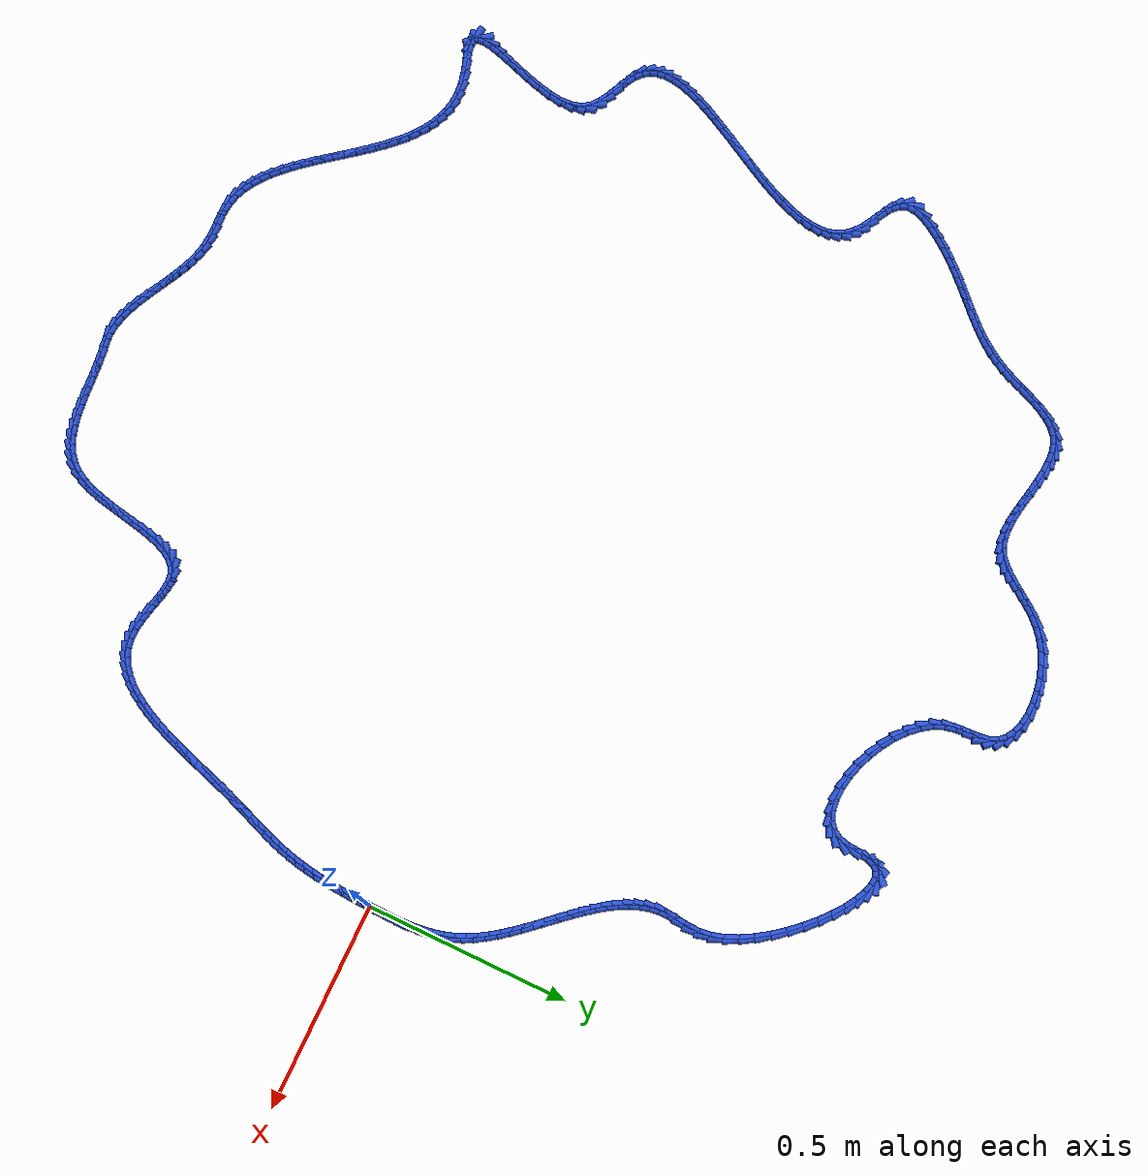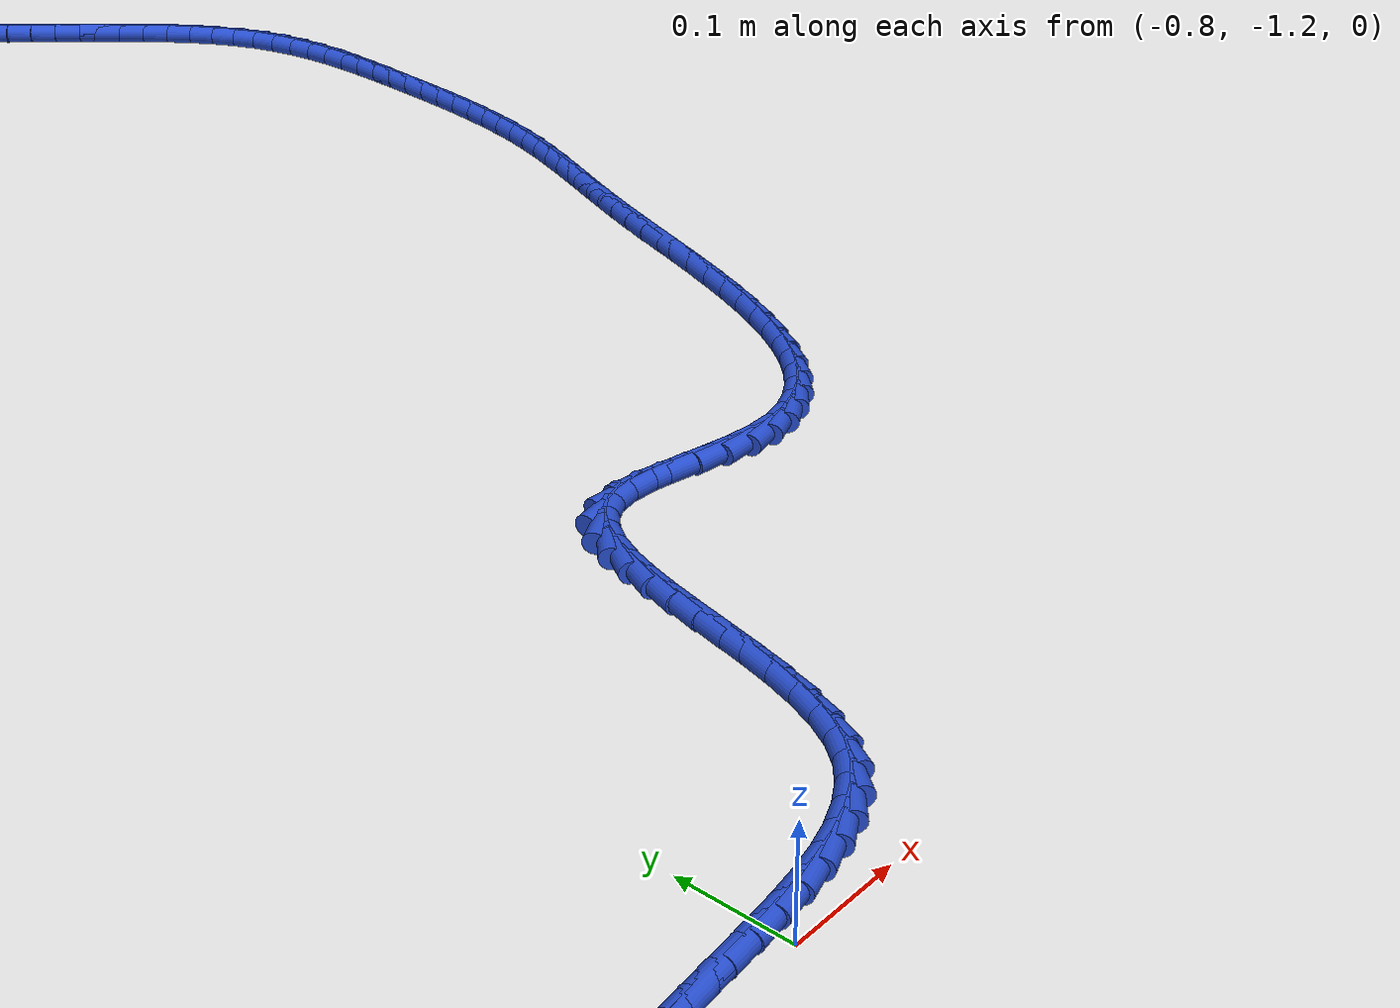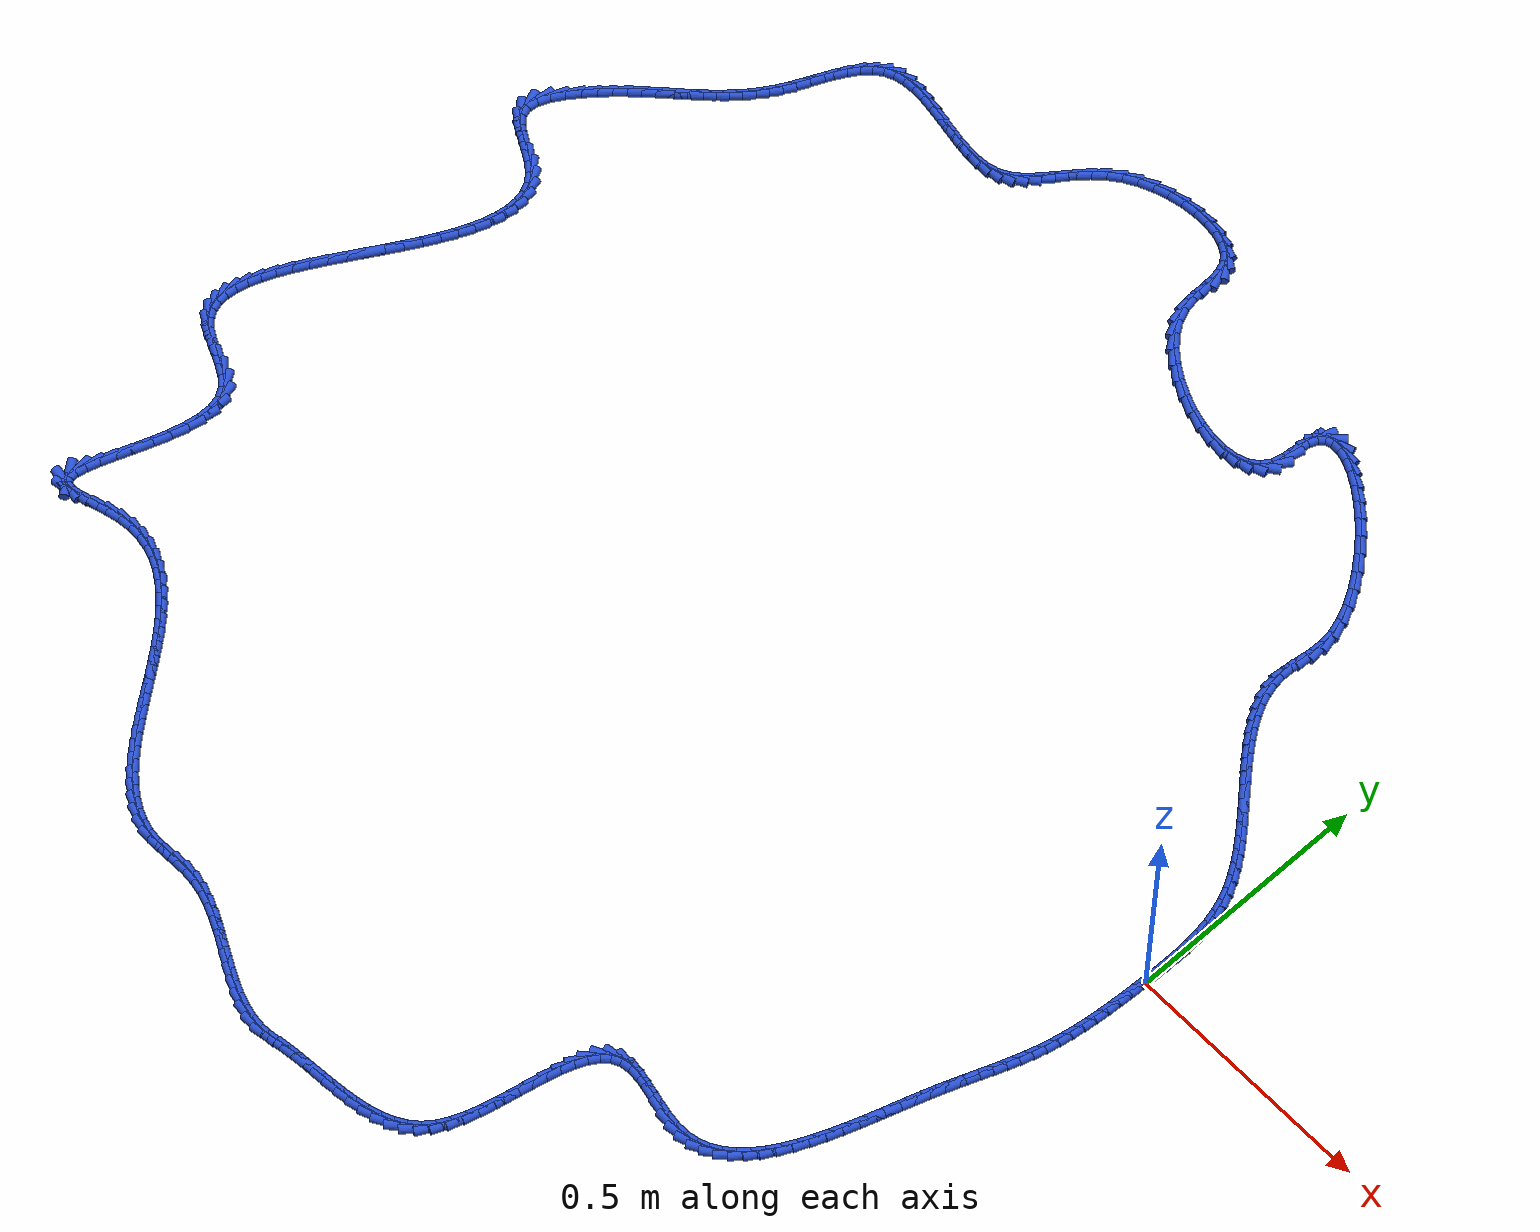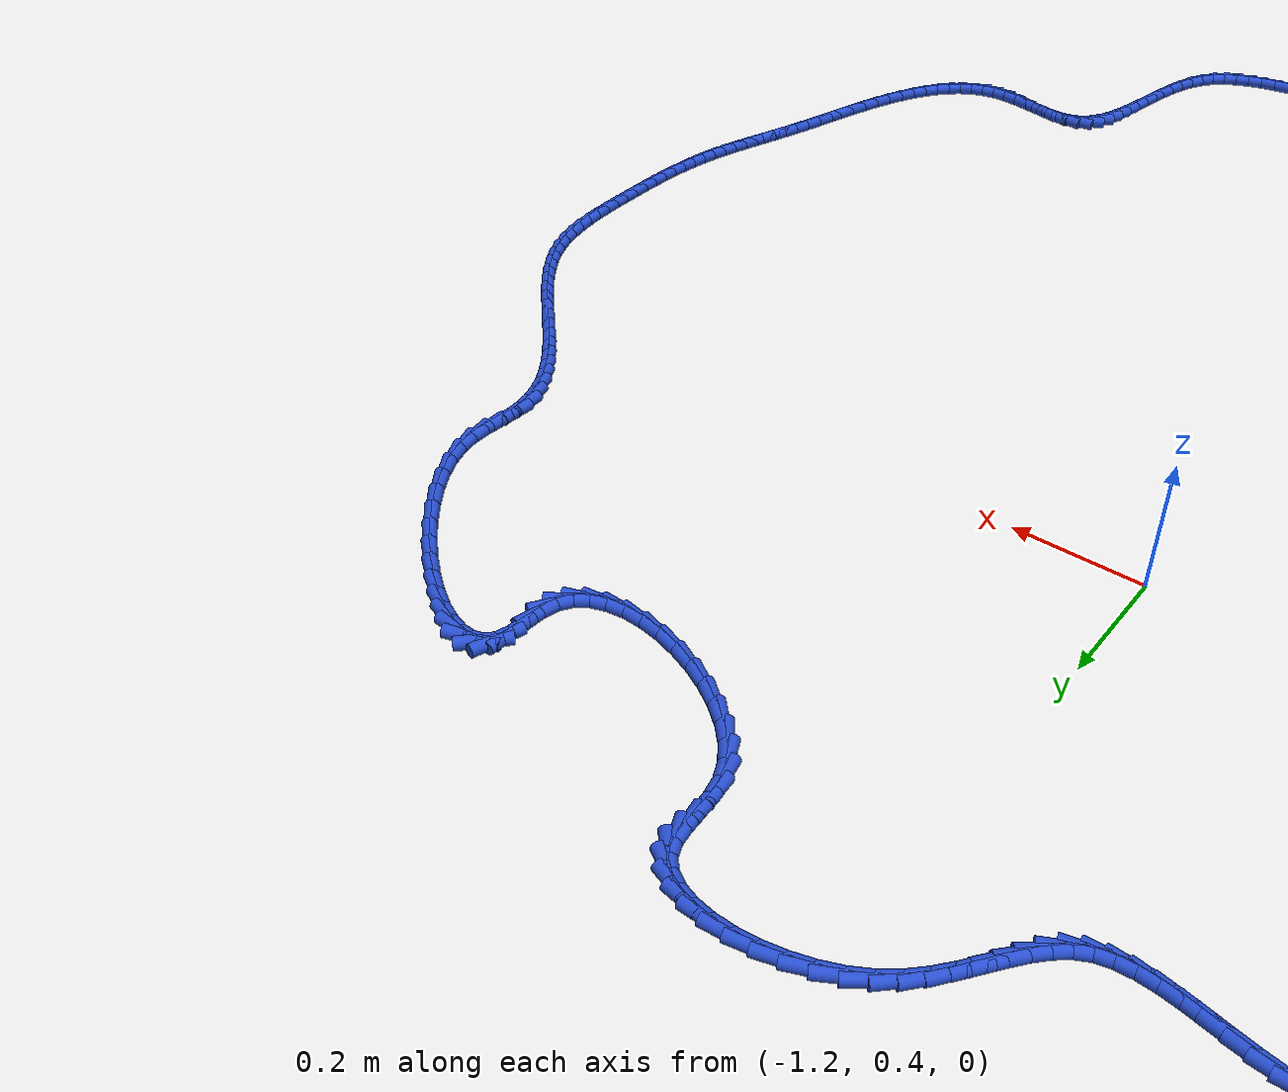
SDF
<sdf version="1.6">
 <world name="default">
  <light name="sun" type="directional">
   <pose>0 0 10 0 -0 0</pose>
   <diffuse>0.8 0.8 0.8 1</diffuse>
   <specular>0.2 0.2 0.2 1</specular>
   <attenuation>
    <range>1000</range>
    <constant>0.9</constant>
    <linear>0.01</linear>
    <quadratic>0.001</quadratic>
   </attenuation>
   <direction>-0.5 0.1 -0.9</direction>
  </light>
  <model name="ground_plane">
   <static>1</static>
   <link name="link">
    <collision name="collision">
     <geometry><plane><normal>0 0 1</normal><size>100 100</size></plane></geometry>
     <surface><friction><ode><mu>100</mu><mu2>50</mu2></ode></friction></surface>
    </collision>
    <visual name="visual">
     <cast_shadows>0</cast_shadows>
     <geometry><plane><normal>0 0 1</normal><size>100 100</size></plane></geometry>
     <material>
      <script><uri>file://media/materials/scripts/gazebo.material</uri><name>Gazebo/WhiteGlow</name></script>
     </material>
    </visual>
   </link>
  </model>
  <gravity>0 0 -9.8</gravity>
  <magnetic_field>6e-06 2.3e-05 -4.2e-05</magnetic_field>
  <atmosphere type="adiabatic"/>
  <physics name="default_physics" default="0" type="ode">
   <max_step_size>0.001</max_step_size>
   <real_time_factor>1</real_time_factor>
   <real_time_update_rate>1000</real_time_update_rate>
  </physics>
  <scene><ambient>0.4 0.4 0.4 1</ambient><background>0.7 0.7 0.7 1</background><shadows>1</shadows></scene>
  <spherical_coordinates>
   <surface_model>EARTH_WGS84</surface_model>
   <latitude_deg>0</latitude_deg>
   <longitude_deg>0</longitude_deg>
   <elevation>0</elevation>
   <heading_deg>0</heading_deg>
  </spherical_coordinates>
  <model name="line">
   <link name="link_0">
    <pose>5.095750210681871e-18 6.938893903907228e-18 0.01 0 1.57 1.5388056076231569</pose>
    <collision name="collision">
     <geometry><cylinder><radius>0.01</radius><length>0.08</length></cylinder></geometry>
    </collision>
    <visual name="visual">
     <material>
      <script><name>Gazebo/Blue</name><uri>file://media/materials/scripts/gazebo.material</uri></script>
     </material>
     <geometry><cylinder><radius>0.01</radius><length>0.08</length></cylinder></geometry>
    </visual>
   </link>
   <link name="link_1">
    <pose>0.0008602382238164219 0.026881069521772712 0.01 0 1.57 1.555280281965907</pose>
    <collision name="collision">
     <geometry><cylinder><radius>0.01</radius><length>0.08</length></cylinder></geometry>
    </collision>
    <visual name="visual">
     <material>
      <script><name>Gazebo/Blue</name><uri>file://media/materials/scripts/gazebo.material</uri></script>
     </material>
     <geometry><cylinder><radius>0.01</radius><length>0.08</length></cylinder></geometry>
    </visual>
   </link>
   <link name="link_2">
    <pose>0.0012765417662471824 0.05370943580001605 0.01 0 1.57 -1.5594066172251986</pose>
    <collision name="collision">
     <geometry><cylinder><radius>0.01</radius><length>0.08</length></cylinder></geometry>
    </collision>
    <visual name="visual">
     <material>
      <script><name>Gazebo/Blue</name><uri>file://media/materials/scripts/gazebo.material</uri></script>
     </material>
     <geometry><cylinder><radius>0.01</radius><length>0.08</length></cylinder></geometry>
    </visual>
   </link>
   <link name="link_3">
    <pose>0.0009725065992423122 0.08040212870797271 0.01 0 1.57 -1.5217017346855326</pose>
    <collision name="collision">
     <geometry><cylinder><radius>0.01</radius><length>0.08</length></cylinder></geometry>
    </collision>
    <visual name="visual">
     <material>
      <script><name>Gazebo/Blue</name><uri>file://media/materials/scripts/gazebo.material</uri></script>
     </material>
     <geometry><cylinder><radius>0.01</radius><length>0.08</length></cylinder></geometry>
    </visual>
   </link>
   <link name="link_4">
    <pose>-0.00032827130524816115 0.10687617811888533 0.01 0 1.57 -1.4727666887338848</pose>
    <collision name="collision">
     <geometry><cylinder><radius>0.01</radius><length>0.08</length></cylinder></geometry>
    </collision>
    <visual name="visual">
     <material>
      <script><name>Gazebo/Blue</name><uri>file://media/materials/scripts/gazebo.material</uri></script>
     </material>
     <geometry><cylinder><radius>0.01</radius><length>0.08</length></cylinder></geometry>
    </visual>
   </link>
   <link name="link_5">
    <pose>-0.0029021959752742127 0.13304861390599657 0.01 0 1.57 -1.4122386485645877</pose>
    <collision name="collision">
     <geometry><cylinder><radius>0.01</radius><length>0.08</length></cylinder></geometry>
    </collision>
    <visual name="visual">
     <material>
      <script><name>Gazebo/Blue</name><uri>file://media/materials/scripts/gazebo.material</uri></script>
     </material>
     <geometry><cylinder><radius>0.01</radius><length>0.08</length></cylinder></geometry>
    </visual>
   </link>
   <link name="link_6">
    <pose>-0.007025671438885812 0.1588364659425492 0.01 0 1.57 -1.3400157972310693</pose>
    <collision name="collision">
     <geometry><cylinder><radius>0.01</radius><length>0.08</length></cylinder></geometry>
    </collision>
    <visual name="visual">
     <material>
      <script><name>Gazebo/Blue</name><uri>file://media/materials/scripts/gazebo.material</uri></script>
     </material>
     <geometry><cylinder><radius>0.01</radius><length>0.08</length></cylinder></geometry>
    </visual>
   </link>
   <link name="link_7">
    <pose>-0.012975101724132937 0.18415676410178572 0.01 0 1.57 -1.2565055473029294</pose>
    <collision name="collision">
     <geometry><cylinder><radius>0.01</radius><length>0.08</length></cylinder></geometry>
    </collision>
    <visual name="visual">
     <material>
      <script><name>Gazebo/Blue</name><uri>file://media/materials/scripts/gazebo.material</uri></script>
     </material>
     <geometry><cylinder><radius>0.01</radius><length>0.08</length></cylinder></geometry>
    </visual>
   </link>
   <link name="link_8">
    <pose>-0.02102689085906555 0.2089265382569489 0.01 0 1.57 -1.1645421362590962</pose>
    <collision name="collision">
     <geometry><cylinder><radius>0.01</radius><length>0.08</length></cylinder></geometry>
    </collision>
    <visual name="visual">
     <material>
      <script><name>Gazebo/Blue</name><uri>file://media/materials/scripts/gazebo.material</uri></script>
     </material>
     <geometry><cylinder><radius>0.01</radius><length>0.08</length></cylinder></geometry>
    </visual>
   </link>
   <link name="link_9">
    <pose>-0.03141463552067935 0.23307369433146488 0.01 0 1.57 -1.0798703875557212</pose>
    <collision name="collision">
     <geometry><cylinder><radius>0.01</radius><length>0.08</length></cylinder></geometry>
    </collision>
    <visual name="visual">
     <material>
      <script><name>Gazebo/Blue</name><uri>file://media/materials/scripts/gazebo.material</uri></script>
     </material>
     <geometry><cylinder><radius>0.01</radius><length>0.08</length></cylinder></geometry>
    </visual>
   </link>
   <link name="link_10">
    <pose>-0.044002037707681595 0.2566201172730296 0.01 0 1.57 -1.0098060208252468</pose>
    <collision name="collision">
     <geometry><cylinder><radius>0.01</radius><length>0.08</length></cylinder></geometry>
    </collision>
    <visual name="visual">
     <material>
      <script><name>Gazebo/Blue</name><uri>file://media/materials/scripts/gazebo.material</uri></script>
     </material>
     <geometry><cylinder><radius>0.01</radius><length>0.08</length></cylinder></geometry>
    </visual>
   </link>
   <link name="link_11">
    <pose>-0.05846347635207173 0.27963579328119625 0.01 0 1.57 -0.9535656398321232</pose>
    <collision name="collision">
     <geometry><cylinder><radius>0.01</radius><length>0.08</length></cylinder></geometry>
    </collision>
    <visual name="visual">
     <material>
      <script><name>Gazebo/Blue</name><uri>file://media/materials/scripts/gazebo.material</uri></script>
     </material>
     <geometry><cylinder><radius>0.01</radius><length>0.08</length></cylinder></geometry>
    </visual>
   </link>
   <link name="link_12">
    <pose>-0.07447179924027313 0.3021910975731917 0.01 0 1.57 -0.9100801353350306</pose>
    <collision name="collision">
     <geometry><cylinder><radius>0.01</radius><length>0.08</length></cylinder></geometry>
    </collision>
    <visual name="visual">
     <material>
      <script><name>Gazebo/Blue</name><uri>file://media/materials/scripts/gazebo.material</uri></script>
     </material>
     <geometry><cylinder><radius>0.01</radius><length>0.08</length></cylinder></geometry>
    </visual>
   </link>
   <link name="link_13">
    <pose>-0.09169985415870918 0.3243564053662428 0.01 0 1.57 -0.8783344374496111</pose>
    <collision name="collision">
     <geometry><cylinder><radius>0.01</radius><length>0.08</length></cylinder></geometry>
    </collision>
    <visual name="visual">
     <material>
      <script><name>Gazebo/Blue</name><uri>file://media/materials/scripts/gazebo.material</uri></script>
     </material>
     <geometry><cylinder><radius>0.01</radius><length>0.08</length></cylinder></geometry>
    </visual>
   </link>
   <link name="link_14">
    <pose>-0.10982048889380337 0.3462020918775764 0.01 0 1.57 -0.8575220311940084</pose>
    <collision name="collision">
     <geometry><cylinder><radius>0.01</radius><length>0.08</length></cylinder></geometry>
    </collision>
    <visual name="visual">
     <material>
      <script><name>Gazebo/Blue</name><uri>file://media/materials/scripts/gazebo.material</uri></script>
     </material>
     <geometry><cylinder><radius>0.01</radius><length>0.08</length></cylinder></geometry>
    </visual>
   </link>
   <link name="link_15">
    <pose>-0.12850655123197896 0.3677985323244192 0.01 0 1.57 -0.8471221855984722</pose>
    <collision name="collision">
     <geometry><cylinder><radius>0.01</radius><length>0.08</length></cylinder></geometry>
    </collision>
    <visual name="visual">
     <material>
      <script><name>Gazebo/Blue</name><uri>file://media/materials/scripts/gazebo.material</uri></script>
     </material>
     <geometry><cylinder><radius>0.01</radius><length>0.08</length></cylinder></geometry>
    </visual>
   </link>
   <link name="link_16">
    <pose>-0.14743088895965947 0.3892161019239984 0.01 0 1.57 -0.8469380375574095</pose>
    <collision name="collision">
     <geometry><cylinder><radius>0.01</radius><length>0.08</length></cylinder></geometry>
    </collision>
    <visual name="visual">
     <material>
      <script><name>Gazebo/Blue</name><uri>file://media/materials/scripts/gazebo.material</uri></script>
     </material>
     <geometry><cylinder><radius>0.01</radius><length>0.08</length></cylinder></geometry>
    </visual>
   </link>
   <link name="link_17">
    <pose>-0.16626634986326816 0.41052517589354054 0.01 0 1.57 -0.8571190771359826</pose>
    <collision name="collision">
     <geometry><cylinder><radius>0.01</radius><length>0.08</length></cylinder></geometry>
    </collision>
    <visual name="visual">
     <material>
      <script><name>Gazebo/Blue</name><uri>file://media/materials/scripts/gazebo.material</uri></script>
     </material>
     <geometry><cylinder><radius>0.01</radius><length>0.08</length></cylinder></geometry>
    </visual>
   </link>
   <link name="link_18">
    <pose>-0.1846857817292285 0.4317961294502726 0.01 0 1.57 -0.8781789403414201</pose>
    <collision name="collision">
     <geometry><cylinder><radius>0.01</radius><length>0.08</length></cylinder></geometry>
    </collision>
    <visual name="visual">
     <material>
      <script><name>Gazebo/Blue</name><uri>file://media/materials/scripts/gazebo.material</uri></script>
     </material>
     <geometry><cylinder><radius>0.01</radius><length>0.08</length></cylinder></geometry>
    </visual>
   </link>
   <link name="link_19">
    <pose>-0.2023620323439639 0.4530993378114214 0.01 0 1.57 -0.9110080031985364</pose>
    <collision name="collision">
     <geometry><cylinder><radius>0.01</radius><length>0.08</length></cylinder></geometry>
    </collision>
    <visual name="visual">
     <material>
      <script><name>Gazebo/Blue</name><uri>file://media/materials/scripts/gazebo.material</uri></script>
     </material>
     <geometry><cylinder><radius>0.01</radius><length>0.08</length></cylinder></geometry>
    </visual>
   </link>
   <link name="link_20">
    <pose>-0.21896794949389778 0.4745051761942138 0.01 0 1.57 -0.956866595205126</pose>
    <collision name="collision">
     <geometry><cylinder><radius>0.01</radius><length>0.08</length></cylinder></geometry>
    </collision>
    <visual name="visual">
     <material>
      <script><name>Gazebo/Blue</name><uri>file://media/materials/scripts/gazebo.material</uri></script>
     </material>
     <geometry><cylinder><radius>0.01</radius><length>0.08</length></cylinder></geometry>
    </visual>
   </link>
   <link name="link_21">
    <pose>-0.23417638096545348 0.49608401981587663 0.01 0 1.57 -1.0173241911575848</pose>
    <collision name="collision">
     <geometry><cylinder><radius>0.01</radius><length>0.08</length></cylinder></geometry>
    </collision>
    <visual name="visual">
     <material>
      <script><name>Gazebo/Blue</name><uri>file://media/materials/scripts/gazebo.material</uri></script>
     </material>
     <geometry><cylinder><radius>0.01</radius><length>0.08</length></cylinder></geometry>
    </visual>
   </link>
   <link name="link_22">
    <pose>-0.2476601745450544 0.5179062438936368 0.01 0 1.57 -1.0940798855237008</pose>
    <collision name="collision">
     <geometry><cylinder><radius>0.01</radius><length>0.08</length></cylinder></geometry>
    </collision>
    <visual name="visual">
     <material>
      <script><name>Gazebo/Blue</name><uri>file://media/materials/scripts/gazebo.material</uri></script>
     </material>
     <geometry><cylinder><radius>0.01</radius><length>0.08</length></cylinder></geometry>
    </visual>
   </link>
   <link name="link_23">
    <pose>-0.25909217801912393 0.540042223644721 0.01 0 1.57 -1.1885678932676573</pose>
    <collision name="collision">
     <geometry><cylinder><radius>0.01</radius><length>0.08</length></cylinder></geometry>
    </collision>
    <visual name="visual">
     <material>
      <script><name>Gazebo/Blue</name><uri>file://media/materials/scripts/gazebo.material</uri></script>
     </material>
     <geometry><cylinder><radius>0.01</radius><length>0.08</length></cylinder></geometry>
    </visual>
   </link>
   <link name="link_24">
    <pose>-0.2681452391740855 0.5625623342863563 0.01 0 1.57 -1.3012591221665977</pose>
    <collision name="collision">
     <geometry><cylinder><radius>0.01</radius><length>0.08</length></cylinder></geometry>
    </collision>
    <visual name="visual">
     <material>
      <script><name>Gazebo/Blue</name><uri>file://media/materials/scripts/gazebo.material</uri></script>
     </material>
     <geometry><cylinder><radius>0.01</radius><length>0.08</length></cylinder></geometry>
    </visual>
   </link>
   <link name="link_25">
    <pose>-0.2744922057963625 0.5855369510357694 0.01 0 1.57 -1.430707616379331</pose>
    <collision name="collision">
     <geometry><cylinder><radius>0.01</radius><length>0.08</length></cylinder></geometry>
    </collision>
    <visual name="visual">
     <material>
      <script><name>Gazebo/Blue</name><uri>file://media/materials/scripts/gazebo.material</uri></script>
     </material>
     <geometry><cylinder><radius>0.01</radius><length>0.08</length></cylinder></geometry>
    </visual>
   </link>
   <link name="link_26">
    <pose>-0.2778059256723784 0.6090364491101872 0.01 0 1.57 1.5697017489471845</pose>
    <collision name="collision">
     <geometry><cylinder><radius>0.01</radius><length>0.08</length></cylinder></geometry>
    </collision>
    <visual name="visual">
     <material>
      <script><name>Gazebo/Blue</name><uri>file://media/materials/scripts/gazebo.material</uri></script>
     </material>
     <geometry><cylinder><radius>0.01</radius><length>0.08</length></cylinder></geometry>
    </visual>
   </link>
   <link name="link_27">
    <pose>-0.27777955023668754 0.6331328852042409 0.01 0 1.57 1.4655885360845564</pose>
    <collision name="collision">
     <geometry><cylinder><radius>0.01</radius><length>0.08</length></cylinder></geometry>
    </collision>
    <visual name="visual">
     <material>
      <script><name>Gazebo/Blue</name><uri>file://media/materials/scripts/gazebo.material</uri></script>
     </material>
     <geometry><cylinder><radius>0.01</radius><length>0.08</length></cylinder></geometry>
    </visual>
   </link>
   <link name="link_28">
    <pose>-0.27515520449582265 0.6579851883493859 0.01 0 1.57 1.4575594987357618</pose>
    <collision name="collision">
     <geometry><cylinder><radius>0.01</radius><length>0.08</length></cylinder></geometry>
    </collision>
    <visual name="visual">
     <material>
      <script><name>Gazebo/Blue</name><uri>file://media/materials/scripts/gazebo.material</uri></script>
     </material>
     <geometry><cylinder><radius>0.01</radius><length>0.08</length></cylinder></geometry>
    </visual>
   </link>
   <link name="link_29">
    <pose>-0.2722104236843385 0.6838794449031096 0.01 0 1.57 1.5390198521601992</pose>
    <collision name="collision">
     <geometry><cylinder><radius>0.01</radius><length>0.08</length></cylinder></geometry>
    </collision>
    <visual name="visual">
     <material>
      <script><name>Gazebo/Blue</name><uri>file://media/materials/scripts/gazebo.material</uri></script>
     </material>
     <geometry><cylinder><radius>0.01</radius><length>0.08</length></cylinder></geometry>
    </visual>
   </link>
   <link name="link_30">
    <pose>-0.27134478253625693 0.7111118481090848 0.01 0 1.57 -1.4479750863037877</pose>
    <collision name="collision">
     <geometry><cylinder><radius>0.01</radius><length>0.08</length></cylinder></geometry>
    </collision>
    <visual name="visual">
     <material>
      <script><name>Gazebo/Blue</name><uri>file://media/materials/scripts/gazebo.material</uri></script>
     </material>
     <geometry><cylinder><radius>0.01</radius><length>0.08</length></cylinder></geometry>
    </visual>
   </link>
   <link name="link_31">
    <pose>-0.2749063172573327 0.7399636006172671 0.01 0 1.57 -1.284787435527426</pose>
    <collision name="collision">
     <geometry><cylinder><radius>0.01</radius><length>0.08</length></cylinder></geometry>
    </collision>
    <visual name="visual">
     <material>
      <script><name>Gazebo/Blue</name><uri>file://media/materials/scripts/gazebo.material</uri></script>
     </material>
     <geometry><cylinder><radius>0.01</radius><length>0.08</length></cylinder></geometry>
    </visual>
   </link>
   <link name="link_32">
    <pose>-0.2838287158932044 0.7703045250992601 0.01 0 1.57 -1.1586155722646712</pose>
    <collision name="collision">
     <geometry><cylinder><radius>0.01</radius><length>0.08</length></cylinder></geometry>
    </collision>
    <visual name="visual">
     <material>
      <script><name>Gazebo/Blue</name><uri>file://media/materials/scripts/gazebo.material</uri></script>
     </material>
     <geometry><cylinder><radius>0.01</radius><length>0.08</length></cylinder></geometry>
    </visual>
   </link>
   <link name="link_33">
    <pose>-0.2974910525555914 0.8015522662803035 0.01 0 1.57 -1.0594826240917112</pose>
    <collision name="collision">
     <geometry><cylinder><radius>0.01</radius><length>0.08</length></cylinder></geometry>
    </collision>
    <visual name="visual">
     <material>
      <script><name>Gazebo/Blue</name><uri>file://media/materials/scripts/gazebo.material</uri></script>
     </material>
     <geometry><cylinder><radius>0.01</radius><length>0.08</length></cylinder></geometry>
    </visual>
   </link>
   <link name="link_34">
    <pose>-0.3151927310190291 0.833101295820823 0.01 0 1.57 -0.9781426358637528</pose>
    <collision name="collision">
     <geometry><cylinder><radius>0.01</radius><length>0.08</length></cylinder></geometry>
    </collision>
    <visual name="visual">
     <material>
      <script><name>Gazebo/Blue</name><uri>file://media/materials/scripts/gazebo.material</uri></script>
     </material>
     <geometry><cylinder><radius>0.01</radius><length>0.08</length></cylinder></geometry>
    </visual>
   </link>
   <link name="link_35">
    <pose>-0.3362331550580526 0.8643460853812431 0.01 0 1.57 -0.9080164408060608</pose>
    <collision name="collision">
     <geometry><cylinder><radius>0.01</radius><length>0.08</length></cylinder></geometry>
    </collision>
    <visual name="visual">
     <material>
      <script><name>Gazebo/Blue</name><uri>file://media/materials/scripts/gazebo.material</uri></script>
     </material>
     <geometry><cylinder><radius>0.01</radius><length>0.08</length></cylinder></geometry>
    </visual>
   </link>
   <link name="link_36">
    <pose>-0.35991172844719765 0.8946811066219895 0.01 0 1.57 -0.8441812483351085</pose>
    <collision name="collision">
     <geometry><cylinder><radius>0.01</radius><length>0.08</length></cylinder></geometry>
    </collision>
    <visual name="visual">
     <material>
      <script><name>Gazebo/Blue</name><uri>file://media/materials/scripts/gazebo.material</uri></script>
     </material>
     <geometry><cylinder><radius>0.01</radius><length>0.08</length></cylinder></geometry>
    </visual>
   </link>
   <link name="link_37">
    <pose>-0.38552785496099934 0.9235008312034867 0.01 0 1.57 -0.7825190281037797</pose>
    <collision name="collision">
     <geometry><cylinder><radius>0.01</radius><length>0.08</length></cylinder></geometry>
    </collision>
    <visual name="visual">
     <material>
      <script><name>Gazebo/Blue</name><uri>file://media/materials/scripts/gazebo.material</uri></script>
     </material>
     <geometry><cylinder><radius>0.01</radius><length>0.08</length></cylinder></geometry>
    </visual>
   </link>
   <link name="link_38">
    <pose>-0.41238093837399276 0.9501997307861596 0.01 0 1.57 -0.7189702375862949</pose>
    <collision name="collision">
     <geometry><cylinder><radius>0.01</radius><length>0.08</length></cylinder></geometry>
    </collision>
    <visual name="visual">
     <material>
      <script><name>Gazebo/Blue</name><uri>file://media/materials/scripts/gazebo.material</uri></script>
     </material>
     <geometry><cylinder><radius>0.01</radius><length>0.08</length></cylinder></geometry>
    </visual>
   </link>
   <link name="link_39">
    <pose>-0.43977038246071365 0.9741722770304336 0.01 0 1.57 -0.6486937677539889</pose>
    <collision name="collision">
     <geometry><cylinder><radius>0.01</radius><length>0.08</length></cylinder></geometry>
    </collision>
    <visual name="visual">
     <material>
      <script><name>Gazebo/Blue</name><uri>file://media/materials/scripts/gazebo.material</uri></script>
     </material>
     <geometry><cylinder><radius>0.01</radius><length>0.08</length></cylinder></geometry>
    </visual>
   </link>
   <link name="link_40">
    <pose>-0.4669955909956972 0.9948129415967332 0.01 0 1.57 -0.5647954215797691</pose>
    <collision name="collision">
     <geometry><cylinder><radius>0.01</radius><length>0.08</length></cylinder></geometry>
    </collision>
    <visual name="visual">
     <material>
      <script><name>Gazebo/Blue</name><uri>file://media/materials/scripts/gazebo.material</uri></script>
     </material>
     <geometry><cylinder><radius>0.01</radius><length>0.08</length></cylinder></geometry>
    </visual>
   </link>
   <link name="link_41">
    <pose>-0.4933559677534789 1.0115161961454842 0.01 0 1.57 -0.45596654985331564</pose>
    <collision name="collision">
     <geometry><cylinder><radius>0.01</radius><length>0.08</length></cylinder></geometry>
    </collision>
    <visual name="visual">
     <material>
      <script><name>Gazebo/Blue</name><uri>file://media/materials/scripts/gazebo.material</uri></script>
     </material>
     <geometry><cylinder><radius>0.01</radius><length>0.08</length></cylinder></geometry>
    </visual>
   </link>
   <link name="link_42">
    <pose>-0.5181509165085937 1.0236765123371103 0.01 0 1.57 -0.30173441285185754</pose>
    <collision name="collision">
     <geometry><cylinder><radius>0.01</radius><length>0.08</length></cylinder></geometry>
    </collision>
    <visual name="visual">
     <material>
      <script><name>Gazebo/Blue</name><uri>file://media/materials/scripts/gazebo.material</uri></script>
     </material>
     <geometry><cylinder><radius>0.01</radius><length>0.08</length></cylinder></geometry>
    </visual>
   </link>
   <link name="link_43">
    <pose>-0.5406798410355771 1.030688361832038 0.01 0 1.57 -0.06421151707830641</pose>
    <collision name="collision">
     <geometry><cylinder><radius>0.01</radius><length>0.08</length></cylinder></geometry>
    </collision>
    <visual name="visual">
     <material>
      <script><name>Gazebo/Blue</name><uri>file://media/materials/scripts/gazebo.material</uri></script>
     </material>
     <geometry><cylinder><radius>0.01</radius><length>0.08</length></cylinder></geometry>
    </visual>
   </link>
   <link name="link_44">
    <pose>-0.5602421451089649 1.0319462162906912 0.01 0 1.57 0.3105724833566927</pose>
    <collision name="collision">
     <geometry><cylinder><radius>0.01</radius><length>0.08</length></cylinder></geometry>
    </collision>
    <visual name="visual">
     <material>
      <script><name>Gazebo/Blue</name><uri>file://media/materials/scripts/gazebo.material</uri></script>
     </material>
     <geometry><cylinder><radius>0.01</radius><length>0.08</length></cylinder></geometry>
    </visual>
   </link>
   <link name="link_45">
    <pose>-0.5761372325032915 1.0268445473734953 0.01 0 1.57 0.8082578855928715</pose>
    <collision name="collision">
     <geometry><cylinder><radius>0.01</radius><length>0.08</length></cylinder></geometry>
    </collision>
    <visual name="visual">
     <material>
      <script><name>Gazebo/Blue</name><uri>file://media/materials/scripts/gazebo.material</uri></script>
     </material>
     <geometry><cylinder><radius>0.01</radius><length>0.08</length></cylinder></geometry>
    </visual>
   </link>
   <link name="link_46">
    <pose>-0.587664506993093 1.0147778267408754 0.01 0 1.57 1.2511273171537673</pose>
    <collision name="collision">
     <geometry><cylinder><radius>0.01</radius><length>0.08</length></cylinder></geometry>
    </collision>
    <visual name="visual">
     <material>
      <script><name>Gazebo/Blue</name><uri>file://media/materials/scripts/gazebo.material</uri></script>
     </material>
     <geometry><cylinder><radius>0.01</radius><length>0.08</length></cylinder></geometry>
    </visual>
   </link>
   <link name="link_47">
    <pose>-0.5941539093810425 0.9951736907397626 0.01 0 1.57 1.4724106238253665</pose>
    <collision name="collision">
     <geometry><cylinder><radius>0.01</radius><length>0.08</length></cylinder></geometry>
    </collision>
    <visual name="visual">
     <material>
      <script><name>Gazebo/Blue</name><uri>file://media/materials/scripts/gazebo.material</uri></script>
     </material>
     <geometry><cylinder><radius>0.01</radius><length>0.08</length></cylinder></geometry>
    </visual>
   </link>
   <link name="link_48">
    <pose>-0.5967002087760224 0.9693764644416092 0.01 0 1.57 1.4845858687058333</pose>
    <collision name="collision">
     <geometry><cylinder><radius>0.01</radius><length>0.08</length></cylinder></geometry>
    </collision>
    <visual name="visual">
     <material>
      <script><name>Gazebo/Blue</name><uri>file://media/materials/scripts/gazebo.material</uri></script>
     </material>
     <geometry><cylinder><radius>0.01</radius><length>0.08</length></cylinder></geometry>
    </visual>
   </link>
   <link name="link_49">
    <pose>-0.5990955950050688 0.9416600020157336 0.01 0 1.57 1.3266898506333262</pose>
    <collision name="collision">
     <geometry><cylinder><radius>0.01</radius><length>0.08</length></cylinder></geometry>
    </collision>
    <visual name="visual">
     <material>
      <script><name>Gazebo/Blue</name><uri>file://media/materials/scripts/gazebo.material</uri></script>
     </material>
     <geometry><cylinder><radius>0.01</radius><length>0.08</length></cylinder></geometry>
    </visual>
   </link>
   <link name="link_50">
    <pose>-0.6053527218246342 0.9165383943744848 0.01 0 1.57 0.9913973601568804</pose>
    <collision name="collision">
     <geometry><cylinder><radius>0.01</radius><length>0.08</length></cylinder></geometry>
    </collision>
    <visual name="visual">
     <material>
      <script><name>Gazebo/Blue</name><uri>file://media/materials/scripts/gazebo.material</uri></script>
     </material>
     <geometry><cylinder><radius>0.01</radius><length>0.08</length></cylinder></geometry>
    </visual>
   </link>
   <link name="link_51">
    <pose>-0.618051778355256 0.8971300693585369 0.01 0 1.57 0.6338707553406878</pose>
    <collision name="collision">
     <geometry><cylinder><radius>0.01</radius><length>0.08</length></cylinder></geometry>
    </collision>
    <visual name="visual">
     <material>
      <script><name>Gazebo/Blue</name><uri>file://media/materials/scripts/gazebo.material</uri></script>
     </material>
     <geometry><cylinder><radius>0.01</radius><length>0.08</length></cylinder></geometry>
    </visual>
   </link>
   <link name="link_52">
    <pose>-0.6366198877525914 0.8834813945151316 0.01 0 1.57 0.3384382736156258</pose>
    <collision name="collision">
     <geometry><cylinder><radius>0.01</radius><length>0.08</length></cylinder></geometry>
    </collision>
    <visual name="visual">
     <material>
      <script><name>Gazebo/Blue</name><uri>file://media/materials/scripts/gazebo.material</uri></script>
     </material>
     <geometry><cylinder><radius>0.01</radius><length>0.08</length></cylinder></geometry>
    </visual>
   </link>
   <link name="link_53">
    <pose>-0.6600641210204116 0.8752294768332636 0.01 0 1.57 0.1172192615195012</pose>
    <collision name="collision">
     <geometry><cylinder><radius>0.01</radius><length>0.08</length></cylinder></geometry>
    </collision>
    <visual name="visual">
     <material>
      <script><name>Gazebo/Blue</name><uri>file://media/materials/scripts/gazebo.material</uri></script>
     </material>
     <geometry><cylinder><radius>0.01</radius><length>0.08</length></cylinder></geometry>
    </visual>
   </link>
   <link name="link_54">
    <pose>-0.687391549162489 0.8720114233019286 0.01 0 1.57 -0.048044682563276875</pose>
    <collision name="collision">
     <geometry><cylinder><radius>0.01</radius><length>0.08</length></cylinder></geometry>
    </collision>
    <visual name="visual">
     <material>
      <script><name>Gazebo/Blue</name><uri>file://media/materials/scripts/gazebo.material</uri></script>
     </material>
     <geometry><cylinder><radius>0.01</radius><length>0.08</length></cylinder></geometry>
    </visual>
   </link>
   <link name="link_55">
    <pose>-0.717609243182596 0.8734643409101216 0.01 0 1.57 -0.17749840947637263</pose>
    <collision name="collision">
     <geometry><cylinder><radius>0.01</radius><length>0.08</length></cylinder></geometry>
    </collision>
    <visual name="visual">
     <material>
      <script><name>Gazebo/Blue</name><uri>file://media/materials/scripts/gazebo.material</uri></script>
     </material>
     <geometry><cylinder><radius>0.01</radius><length>0.08</length></cylinder></geometry>
    </visual>
   </link>
   <link name="link_56">
    <pose>-0.7497242740845045 0.8792253366468377 0.01 0 1.57 -0.2859003919538598</pose>
    <collision name="collision">
     <geometry><cylinder><radius>0.01</radius><length>0.08</length></cylinder></geometry>
    </collision>
    <visual name="visual">
     <material>
      <script><name>Gazebo/Blue</name><uri>file://media/materials/scripts/gazebo.material</uri></script>
     </material>
     <geometry><cylinder><radius>0.01</radius><length>0.08</length></cylinder></geometry>
    </visual>
   </link>
   <link name="link_57">
    <pose>-0.7827437128719864 0.8889315175010721 0.01 0 1.57 -0.38354210900078095</pose>
    <collision name="collision">
     <geometry><cylinder><radius>0.01</radius><length>0.08</length></cylinder></geometry>
    </collision>
    <visual name="visual">
     <material>
      <script><name>Gazebo/Blue</name><uri>file://media/materials/scripts/gazebo.material</uri></script>
     </material>
     <geometry><cylinder><radius>0.01</radius><length>0.08</length></cylinder></geometry>
    </visual>
   </link>
   <link name="link_58">
    <pose>-0.8156746305488141 0.9022199904618203 0.01 0 1.57 -0.4781874516379408</pose>
    <collision name="collision">
     <geometry><cylinder><radius>0.01</radius><length>0.08</length></cylinder></geometry>
    </collision>
    <visual name="visual">
     <material>
      <script><name>Gazebo/Blue</name><uri>file://media/materials/scripts/gazebo.material</uri></script>
     </material>
     <geometry><cylinder><radius>0.01</radius><length>0.08</length></cylinder></geometry>
    </visual>
   </link>
   <link name="link_59">
    <pose>-0.8475240981187592 0.918727862518077 0.01 0 1.57 -0.5766247520935476</pose>
    <collision name="collision">
     <geometry><cylinder><radius>0.01</radius><length>0.08</length></cylinder></geometry>
    </collision>
    <visual name="visual">
     <material>
      <script><name>Gazebo/Blue</name><uri>file://media/materials/scripts/gazebo.material</uri></script>
     </material>
     <geometry><cylinder><radius>0.01</radius><length>0.08</length></cylinder></geometry>
    </visual>
   </link>
   <link name="link_60">
    <pose>-0.8772991865855945 0.9380922406588379 0.01 0 1.57 -0.6858678982872373</pose>
    <collision name="collision">
     <geometry><cylinder><radius>0.01</radius><length>0.08</length></cylinder></geometry>
    </collision>
    <visual name="visual">
     <material>
      <script><name>Gazebo/Blue</name><uri>file://media/materials/scripts/gazebo.material</uri></script>
     </material>
     <geometry><cylinder><radius>0.01</radius><length>0.08</length></cylinder></geometry>
    </visual>
   </link>
   <link name="link_61">
    <pose>-0.9040069669530918 0.9599502318730978 0.01 0 1.57 -0.8141482951205399</pose>
    <collision name="collision">
     <geometry><cylinder><radius>0.01</radius><length>0.08</length></cylinder></geometry>
    </collision>
    <visual name="visual">
     <material>
      <script><name>Gazebo/Blue</name><uri>file://media/materials/scripts/gazebo.material</uri></script>
     </material>
     <geometry><cylinder><radius>0.01</radius><length>0.08</length></cylinder></geometry>
    </visual>
   </link>
   <link name="link_62">
    <pose>-0.926654510225023 0.9839389431498518 0.01 0 1.57 -0.9715006474244978</pose>
    <collision name="collision">
     <geometry><cylinder><radius>0.01</radius><length>0.08</length></cylinder></geometry>
    </collision>
    <visual name="visual">
     <material>
      <script><name>Gazebo/Blue</name><uri>file://media/materials/scripts/gazebo.material</uri></script>
     </material>
     <geometry><cylinder><radius>0.01</radius><length>0.08</length></cylinder></geometry>
    </visual>
   </link>
   <link name="link_63">
    <pose>-0.9442488874051604 1.0096954814780954 0.01 0 1.57 -1.1686511473507128</pose>
    <collision name="collision">
     <geometry><cylinder><radius>0.01</radius><length>0.08</length></cylinder></geometry>
    </collision>
    <visual name="visual">
     <material>
      <script><name>Gazebo/Blue</name><uri>file://media/materials/scripts/gazebo.material</uri></script>
     </material>
     <geometry><cylinder><radius>0.01</radius><length>0.08</length></cylinder></geometry>
    </visual>
   </link>
   <link name="link_64">
    <pose>-0.9558009994639148 1.0368562055137212 0.01 0 1.57 -1.3749422259213553</pose>
    <collision name="collision">
     <geometry><cylinder><radius>0.01</radius><length>0.08</length></cylinder></geometry>
    </collision>
    <visual name="visual">
     <material>
      <script><name>Gazebo/Blue</name><uri>file://media/materials/scripts/gazebo.material</uri></script>
     </material>
     <geometry><cylinder><radius>0.01</radius><length>0.08</length></cylinder></geometry>
    </visual>
   </link>
   <link name="link_65">
    <pose>-0.9613559659750638 1.0648553990411243 0.01 0 1.57 -1.4978799357225159</pose>
    <collision name="collision">
     <geometry><cylinder><radius>0.01</radius><length>0.08</length></cylinder></geometry>
    </collision>
    <visual name="visual">
     <material>
      <script><name>Gazebo/Blue</name><uri>file://media/materials/scripts/gazebo.material</uri></script>
     </material>
     <geometry><cylinder><radius>0.01</radius><length>0.08</length></cylinder></geometry>
    </visual>
   </link>
   <link name="link_66">
    <pose>-0.9633864685604215 1.0926530270814234 0.01 0 1.57 -1.5207536580775673</pose>
    <collision name="collision">
     <geometry><cylinder><radius>0.01</radius><length>0.08</length></cylinder></geometry>
    </collision>
    <visual name="visual">
     <material>
      <script><name>Gazebo/Blue</name><uri>file://media/materials/scripts/gazebo.material</uri></script>
     </material>
     <geometry><cylinder><radius>0.01</radius><length>0.08</length></cylinder></geometry>
    </visual>
   </link>
   <link name="link_67">
    <pose>-0.9647131087710531 1.1191410749512856 0.01 0 1.57 -1.428706162045194</pose>
    <collision name="collision">
     <geometry><cylinder><radius>0.01</radius><length>0.08</length></cylinder></geometry>
    </collision>
    <visual name="visual">
     <material>
      <script><name>Gazebo/Blue</name><uri>file://media/materials/scripts/gazebo.material</uri></script>
     </material>
     <geometry><cylinder><radius>0.01</radius><length>0.08</length></cylinder></geometry>
    </visual>
   </link>
   <link name="link_68">
    <pose>-0.9681564881580238 1.1432115279673774 0.01 0 1.57 -1.1849644542502096</pose>
    <collision name="collision">
     <geometry><cylinder><radius>0.01</radius><length>0.08</length></cylinder></geometry>
    </collision>
    <visual name="visual">
     <material>
      <script><name>Gazebo/Blue</name><uri>file://media/materials/scripts/gazebo.material</uri></script>
     </material>
     <geometry><cylinder><radius>0.01</radius><length>0.08</length></cylinder></geometry>
    </visual>
   </link>
   <link name="link_69">
    <pose>-0.976505747035601 1.1637665441024576 0.01 0 1.57 -0.8460024315804001</pose>
    <collision name="collision">
     <geometry><cylinder><radius>0.01</radius><length>0.08</length></cylinder></geometry>
    </collision>
    <visual name="visual">
     <material>
      <script><name>Gazebo/Blue</name><uri>file://media/materials/scripts/gazebo.material</uri></script>
     </material>
     <geometry><cylinder><radius>0.01</radius><length>0.08</length></cylinder></geometry>
    </visual>
   </link>
   <link name="link_70">
    <pose>-0.9910523636938523 1.180192534405879 0.01 0 1.57 -0.5558084752771331</pose>
    <collision name="collision">
     <geometry><cylinder><radius>0.01</radius><length>0.08</length></cylinder></geometry>
    </collision>
    <visual name="visual">
     <material>
      <script><name>Gazebo/Blue</name><uri>file://media/materials/scripts/gazebo.material</uri></script>
     </material>
     <geometry><cylinder><radius>0.01</radius><length>0.08</length></cylinder></geometry>
    </visual>
   </link>
   <link name="link_71">
    <pose>-1.0109666038102227 1.1925617814501899 0.01 0 1.57 -0.3342853103051633</pose>
    <collision name="collision">
     <geometry><cylinder><radius>0.01</radius><length>0.08</length></cylinder></geometry>
    </collision>
    <visual name="visual">
     <material>
      <script><name>Gazebo/Blue</name><uri>file://media/materials/scripts/gazebo.material</uri></script>
     </material>
     <geometry><cylinder><radius>0.01</radius><length>0.08</length></cylinder></geometry>
    </visual>
   </link>
   <link name="link_72">
    <pose>-1.035257805652852 1.2009986019730625 0.01 0 1.57 -0.16570383894547938</pose>
    <collision name="collision">
     <geometry><cylinder><radius>0.01</radius><length>0.08</length></cylinder></geometry>
    </collision>
    <visual name="visual">
     <material>
      <script><name>Gazebo/Blue</name><uri>file://media/materials/scripts/gazebo.material</uri></script>
     </material>
     <geometry><cylinder><radius>0.01</radius><length>0.08</length></cylinder></geometry>
    </visual>
   </link>
   <link name="link_73">
    <pose>-1.0629353074898786 1.2056273127121695 0.01 0 1.57 -0.03141031880779321</pose>
    <collision name="collision">
     <geometry><cylinder><radius>0.01</radius><length>0.08</length></cylinder></geometry>
    </collision>
    <visual name="visual">
     <material>
      <script><name>Gazebo/Blue</name><uri>file://media/materials/scripts/gazebo.material</uri></script>
     </material>
     <geometry><cylinder><radius>0.01</radius><length>0.08</length></cylinder></geometry>
    </visual>
   </link>
   <link name="link_74">
    <pose>-1.093008447589441 1.2065722304051816 0.01 0 1.57 0.08286934360039021</pose>
    <collision name="collision">
     <geometry><cylinder><radius>0.01</radius><length>0.08</length></cylinder></geometry>
    </collision>
    <visual name="visual">
     <material>
      <script><name>Gazebo/Blue</name><uri>file://media/materials/scripts/gazebo.material</uri></script>
     </material>
     <geometry><cylinder><radius>0.01</radius><length>0.08</length></cylinder></geometry>
    </visual>
   </link>
   <link name="link_75">
    <pose>-1.1244865642196784 1.2039576717897713 0.01 0 1.57 0.1874640280628882</pose>
    <collision name="collision">
     <geometry><cylinder><radius>0.01</radius><length>0.08</length></cylinder></geometry>
    </collision>
    <visual name="visual">
     <material>
      <script><name>Gazebo/Blue</name><uri>file://media/materials/scripts/gazebo.material</uri></script>
     </material>
     <geometry><cylinder><radius>0.01</radius><length>0.08</length></cylinder></geometry>
    </visual>
   </link>
   <link name="link_76">
    <pose>-1.1563789956487294 1.1979079536036106 0.01 0 1.57 0.29045268991197265</pose>
    <collision name="collision">
     <geometry><cylinder><radius>0.01</radius><length>0.08</length></cylinder></geometry>
    </collision>
    <visual name="visual">
     <material>
      <script><name>Gazebo/Blue</name><uri>file://media/materials/scripts/gazebo.material</uri></script>
     </material>
     <geometry><cylinder><radius>0.01</radius><length>0.08</length></cylinder></geometry>
    </visual>
   </link>
   <link name="link_77">
    <pose>-1.1876950801447332 1.1885473925843708 0.01 0 1.57 0.3991264765575888</pose>
    <collision name="collision">
     <geometry><cylinder><radius>0.01</radius><length>0.08</length></cylinder></geometry>
    </collision>
    <visual name="visual">
     <material>
      <script><name>Gazebo/Blue</name><uri>file://media/materials/scripts/gazebo.material</uri></script>
     </material>
     <geometry><cylinder><radius>0.01</radius><length>0.08</length></cylinder></geometry>
    </visual>
   </link>
   <link name="link_78">
    <pose>-1.2174441559758291 1.1760003054697243 0.01 0 1.57 0.5211219778421812</pose>
    <collision name="collision">
     <geometry><cylinder><radius>0.01</radius><length>0.08</length></cylinder></geometry>
    </collision>
    <visual name="visual">
     <material>
      <script><name>Gazebo/Blue</name><uri>file://media/materials/scripts/gazebo.material</uri></script>
     </material>
     <geometry><cylinder><radius>0.01</radius><length>0.08</length></cylinder></geometry>
    </visual>
   </link>
   <link name="link_79">
    <pose>-1.2446355614101559 1.1603910089973428 0.01 0 1.57 0.6593469376571012</pose>
    <collision name="collision">
     <geometry><cylinder><radius>0.01</radius><length>0.08</length></cylinder></geometry>
    </collision>
    <visual name="visual">
     <material>
      <script><name>Gazebo/Blue</name><uri>file://media/materials/scripts/gazebo.material</uri></script>
     </material>
     <geometry><cylinder><radius>0.01</radius><length>0.08</length></cylinder></geometry>
    </visual>
   </link>
   <link name="link_80">
    <pose>-1.268460172441999 1.1419255294227955 0.01 0 1.57 0.7816400615174119</pose>
    <collision name="collision">
     <geometry><cylinder><radius>0.01</radius><length>0.08</length></cylinder></geometry>
    </collision>
    <visual name="visual">
     <material>
      <script><name>Gazebo/Blue</name><uri>file://media/materials/scripts/gazebo.material</uri></script>
     </material>
     <geometry><cylinder><radius>0.01</radius><length>0.08</length></cylinder></geometry>
    </visual>
   </link>
   <link name="link_81">
    <pose>-1.2892277237875105 1.121313487536508 0.01 0 1.57 0.869834839244422</pose>
    <collision name="collision">
     <geometry><cylinder><radius>0.01</radius><length>0.08</length></cylinder></geometry>
    </collision>
    <visual name="visual">
     <material>
      <script><name>Gazebo/Blue</name><uri>file://media/materials/scripts/gazebo.material</uri></script>
     </material>
     <geometry><cylinder><radius>0.01</radius><length>0.08</length></cylinder></geometry>
    </visual>
   </link>
   <link name="link_82">
    <pose>-1.307673826097418 1.0994561894498418 0.01 0 1.57 0.9212562566497868</pose>
    <collision name="collision">
     <geometry><cylinder><radius>0.01</radius><length>0.08</length></cylinder></geometry>
    </collision>
    <visual name="visual">
     <material>
      <script><name>Gazebo/Blue</name><uri>file://media/materials/scripts/gazebo.material</uri></script>
     </material>
     <geometry><cylinder><radius>0.01</radius><length>0.08</length></cylinder></geometry>
    </visual>
   </link>
   <link name="link_83">
    <pose>-1.324534921837413 1.077255315671264 0.01 0 1.57 0.9338190762296164</pose>
    <collision name="collision">
     <geometry><cylinder><radius>0.01</radius><length>0.08</length></cylinder></geometry>
    </collision>
    <visual name="visual">
     <material>
      <script><name>Gazebo/Blue</name><uri>file://media/materials/scripts/gazebo.material</uri></script>
     </material>
     <geometry><cylinder><radius>0.01</radius><length>0.08</length></cylinder></geometry>
    </visual>
   </link>
   <link name="link_84">
    <pose>-1.3405474534731863 1.0556125467092436 0.01 0 1.57 0.9035309947150487</pose>
    <collision name="collision">
     <geometry><cylinder><radius>0.01</radius><length>0.08</length></cylinder></geometry>
    </collision>
    <visual name="visual">
     <material>
      <script><name>Gazebo/Blue</name><uri>file://media/materials/scripts/gazebo.material</uri></script>
     </material>
     <geometry><cylinder><radius>0.01</radius><length>0.08</length></cylinder></geometry>
    </visual>
   </link>
   <link name="link_85">
    <pose>-1.3564478634704278 1.0354295630722483 0.01 0 1.57 0.8231365293390003</pose>
    <collision name="collision">
     <geometry><cylinder><radius>0.01</radius><length>0.08</length></cylinder></geometry>
    </collision>
    <visual name="visual">
     <material>
      <script><name>Gazebo/Blue</name><uri>file://media/materials/scripts/gazebo.material</uri></script>
     </material>
     <geometry><cylinder><radius>0.01</radius><length>0.08</length></cylinder></geometry>
    </visual>
   </link>
   <link name="link_86">
    <pose>-1.3729725942948297 1.0176080452687455 0.01 0 1.57 0.6832052717225015</pose>
    <collision name="collision">
     <geometry><cylinder><radius>0.01</radius><length>0.08</length></cylinder></geometry>
    </collision>
    <visual name="visual">
     <material>
      <script><name>Gazebo/Blue</name><uri>file://media/materials/scripts/gazebo.material</uri></script>
     </material>
     <geometry><cylinder><radius>0.01</radius><length>0.08</length></cylinder></geometry>
    </visual>
   </link>
   <link name="link_87">
    <pose>-1.3908580884120818 1.0030496738072034 0.01 0 1.57 0.4796244364752886</pose>
    <collision name="collision">
     <geometry><cylinder><radius>0.01</radius><length>0.08</length></cylinder></geometry>
    </collision>
    <visual name="visual">
     <material>
      <script><name>Gazebo/Blue</name><uri>file://media/materials/scripts/gazebo.material</uri></script>
     </material>
     <geometry><cylinder><radius>0.01</radius><length>0.08</length></cylinder></geometry>
    </visual>
   </link>
   <link name="link_88">
    <pose>-1.4108407232222935 0.9926560343684857 0.01 0 1.57 0.24694636733877406</pose>
    <collision name="collision">
     <geometry><cylinder><radius>0.01</radius><length>0.08</length></cylinder></geometry>
    </collision>
    <visual name="visual">
     <material>
      <script><name>Gazebo/Blue</name><uri>file://media/materials/scripts/gazebo.material</uri></script>
     </material>
     <geometry><cylinder><radius>0.01</radius><length>0.08</length></cylinder></geometry>
    </visual>
   </link>
   <link name="link_89">
    <pose>-1.4334085932479042 0.9869668612557813 0.01 0 1.57 0.06535604649514655</pose>
    <collision name="collision">
     <geometry><cylinder><radius>0.01</radius><length>0.08</length></cylinder></geometry>
    </collision>
    <visual name="visual">
     <material>
      <script><name>Gazebo/Blue</name><uri>file://media/materials/scripts/gazebo.material</uri></script>
     </material>
     <geometry><cylinder><radius>0.01</radius><length>0.08</length></cylinder></geometry>
    </visual>
   </link>
   <link name="link_90">
    <pose>-1.4582399871167897 0.9853416649028445 0.01 0 1.57 -0.05848861458791421</pose>
    <collision name="collision">
     <geometry><cylinder><radius>0.01</radius><length>0.08</length></cylinder></geometry>
    </collision>
    <visual name="visual">
     <material>
      <script><name>Gazebo/Blue</name><uri>file://media/materials/scripts/gazebo.material</uri></script>
     </material>
     <geometry><cylinder><radius>0.01</radius><length>0.08</length></cylinder></geometry>
    </visual>
   </link>
   <link name="link_91">
    <pose>-1.484848362843575 0.9868997290107299 0.01 0 1.57 -0.13750568170730054</pose>
    <collision name="collision">
     <geometry><cylinder><radius>0.01</radius><length>0.08</length></cylinder></geometry>
    </collision>
    <visual name="visual">
     <material>
      <script><name>Gazebo/Blue</name><uri>file://media/materials/scripts/gazebo.material</uri></script>
     </material>
     <geometry><cylinder><radius>0.01</radius><length>0.08</length></cylinder></geometry>
    </visual>
   </link>
   <link name="link_92">
    <pose>-1.5127471784428845 0.9907603372804923 0.01 0 1.57 -0.18200299643530365</pose>
    <collision name="collision">
     <geometry><cylinder><radius>0.01</radius><length>0.08</length></cylinder></geometry>
    </collision>
    <visual name="visual">
     <material>
      <script><name>Gazebo/Blue</name><uri>file://media/materials/scripts/gazebo.material</uri></script>
     </material>
     <geometry><cylinder><radius>0.01</radius><length>0.08</length></cylinder></geometry>
    </visual>
   </link>
   <link name="link_93">
    <pose>-1.5414498919293462 0.9960427734131877 0.01 0 1.57 -0.19804270112448627</pose>
    <collision name="collision">
     <geometry><cylinder><radius>0.01</radius><length>0.08</length></cylinder></geometry>
    </collision>
    <visual name="visual">
     <material>
      <script><name>Gazebo/Blue</name><uri>file://media/materials/scripts/gazebo.material</uri></script>
     </material>
     <geometry><cylinder><radius>0.01</radius><length>0.08</length></cylinder></geometry>
    </visual>
   </link>
   <link name="link_94">
    <pose>-1.5704699613175832 1.0018663211098708 0.01 0 1.57 -0.187838056191122</pose>
    <collision name="collision">
     <geometry><cylinder><radius>0.01</radius><length>0.08</length></cylinder></geometry>
    </collision>
    <visual name="visual">
     <material>
      <script><name>Gazebo/Blue</name><uri>file://media/materials/scripts/gazebo.material</uri></script>
     </material>
     <geometry><cylinder><radius>0.01</radius><length>0.08</length></cylinder></geometry>
    </visual>
   </link>
   <link name="link_95">
    <pose>-1.599320844622222 1.0073502640715961 0.01 0 1.57 -0.15008117304217702</pose>
    <collision name="collision">
     <geometry><cylinder><radius>0.01</radius><length>0.08</length></cylinder></geometry>
    </collision>
    <visual name="visual">
     <material>
      <script><name>Gazebo/Blue</name><uri>file://media/materials/scripts/gazebo.material</uri></script>
     </material>
     <geometry><cylinder><radius>0.01</radius><length>0.08</length></cylinder></geometry>
    </visual>
   </link>
   <link name="link_96">
    <pose>-1.6275159998578874 1.0116138859994195 0.01 0 1.57 -0.07976952049292627</pose>
    <collision name="collision">
     <geometry><cylinder><radius>0.01</radius><length>0.08</length></cylinder></geometry>
    </collision>
    <visual name="visual">
     <material>
      <script><name>Gazebo/Blue</name><uri>file://media/materials/scripts/gazebo.material</uri></script>
     </material>
     <geometry><cylinder><radius>0.01</radius><length>0.08</length></cylinder></geometry>
    </visual>
   </link>
   <link name="link_97">
    <pose>-1.6545688850392049 1.0137764705943952 0.01 0 1.57 0.032209069625093664</pose>
    <collision name="collision">
     <geometry><cylinder><radius>0.01</radius><length>0.08</length></cylinder></geometry>
    </collision>
    <visual name="visual">
     <material>
      <script><name>Gazebo/Blue</name><uri>file://media/materials/scripts/gazebo.material</uri></script>
     </material>
     <geometry><cylinder><radius>0.01</radius><length>0.08</length></cylinder></geometry>
    </visual>
   </link>
   <link name="link_98">
    <pose>-1.6799929581807995 1.0129573015575788 0.01 0 1.57 0.19821614559104989</pose>
    <collision name="collision">
     <geometry><cylinder><radius>0.01</radius><length>0.08</length></cylinder></geometry>
    </collision>
    <visual name="visual">
     <material>
      <script><name>Gazebo/Blue</name><uri>file://media/materials/scripts/gazebo.material</uri></script>
     </material>
     <geometry><cylinder><radius>0.01</radius><length>0.08</length></cylinder></geometry>
    </visual>
   </link>
   <link name="link_99">
    <pose>-1.7033016772972975 1.0082756625900253 0.01 0 1.57 0.4268867244522433</pose>
    <collision name="collision">
     <geometry><cylinder><radius>0.01</radius><length>0.08</length></cylinder></geometry>
    </collision>
    <visual name="visual">
     <material>
      <script><name>Gazebo/Blue</name><uri>file://media/materials/scripts/gazebo.material</uri></script>
     </material>
     <geometry><cylinder><radius>0.01</radius><length>0.08</length></cylinder></geometry>
    </visual>
   </link>
   <link name="link_100">
    <pose>-1.7240112265048468 0.9988557525972179 0.01 0 1.57 0.6782457143143431</pose>
    <collision name="collision">
     <geometry><cylinder><radius>0.01</radius><length>0.08</length></cylinder></geometry>
    </collision>
    <visual name="visual">
     <material>
      <script><name>Gazebo/Blue</name><uri>file://media/materials/scripts/gazebo.material</uri></script>
     </material>
     <geometry><cylinder><radius>0.01</radius><length>0.08</length></cylinder></geometry>
    </visual>
   </link>
   <link name="link_101">
    <pose>-1.7419563801029105 0.9843961936548536 0.01 0 1.57 0.8745279619483493</pose>
    <collision name="collision">
     <geometry><cylinder><radius>0.01</radius><length>0.08</length></cylinder></geometry>
    </collision>
    <visual name="visual">
     <material>
      <script><name>Gazebo/Blue</name><uri>file://media/materials/scripts/gazebo.material</uri></script>
     </material>
     <geometry><cylinder><radius>0.01</radius><length>0.08</length></cylinder></geometry>
    </visual>
   </link>
   <link name="link_102">
    <pose>-1.7575846920861433 0.9657004593801831 0.01 0 1.57 1.0096930201901795</pose>
    <collision name="collision">
     <geometry><cylinder><radius>0.01</radius><length>0.08</length></cylinder></geometry>
    </collision>
    <visual name="visual">
     <material>
      <script><name>Gazebo/Blue</name><uri>file://media/materials/scripts/gazebo.material</uri></script>
     </material>
     <geometry><cylinder><radius>0.01</radius><length>0.08</length></cylinder></geometry>
    </visual>
   </link>
   <link name="link_103">
    <pose>-1.771413294853627 0.9436974743608334 0.01 0 1.57 1.0955564072837047</pose>
    <collision name="collision">
     <geometry><cylinder><radius>0.01</radius><length>0.08</length></cylinder></geometry>
    </collision>
    <visual name="visual">
     <material>
      <script><name>Gazebo/Blue</name><uri>file://media/materials/scripts/gazebo.material</uri></script>
     </material>
     <geometry><cylinder><radius>0.01</radius><length>0.08</length></cylinder></geometry>
    </visual>
   </link>
   <link name="link_104">
    <pose>-1.7839593208044442 0.919316163184432 0.01 0 1.57 1.142907080044236</pose>
    <collision name="collision">
     <geometry><cylinder><radius>0.01</radius><length>0.08</length></cylinder></geometry>
    </collision>
    <visual name="visual">
     <material>
      <script><name>Gazebo/Blue</name><uri>file://media/materials/scripts/gazebo.material</uri></script>
     </material>
     <geometry><cylinder><radius>0.01</radius><length>0.08</length></cylinder></geometry>
    </visual>
   </link>
   <link name="link_105">
    <pose>-1.7957399023376763 0.8934854504386062 0.01 0 1.57 1.158270458247874</pose>
    <collision name="collision">
     <geometry><cylinder><radius>0.01</radius><length>0.08</length></cylinder></geometry>
    </collision>
    <visual name="visual">
     <material>
      <script><name>Gazebo/Blue</name><uri>file://media/materials/scripts/gazebo.material</uri></script>
     </material>
     <geometry><cylinder><radius>0.01</radius><length>0.08</length></cylinder></geometry>
    </visual>
   </link>
   <link name="link_106">
    <pose>-1.8072721718524052 0.8671342607109827 0.01 0 1.57 1.143883452726162</pose>
    <collision name="collision">
     <geometry><cylinder><radius>0.01</radius><length>0.08</length></cylinder></geometry>
    </collision>
    <visual name="visual">
     <material>
      <script><name>Gazebo/Blue</name><uri>file://media/materials/scripts/gazebo.material</uri></script>
     </material>
     <geometry><cylinder><radius>0.01</radius><length>0.08</length></cylinder></geometry>
    </visual>
   </link>
   <link name="link_107">
    <pose>-1.8190732617477121 0.8411915185891887 0.01 0 1.57 1.0981838672136532</pose>
    <collision name="collision">
     <geometry><cylinder><radius>0.01</radius><length>0.08</length></cylinder></geometry>
    </collision>
    <visual name="visual">
     <material>
      <script><name>Gazebo/Blue</name><uri>file://media/materials/scripts/gazebo.material</uri></script>
     </material>
     <geometry><cylinder><radius>0.01</radius><length>0.08</length></cylinder></geometry>
    </visual>
   </link>
   <link name="link_108">
    <pose>-1.8316565989515088 0.8165789625388601 0.01 0 1.57 1.0314010881256435</pose>
    <collision name="collision">
     <geometry><cylinder><radius>0.01</radius><length>0.08</length></cylinder></geometry>
    </collision>
    <visual name="visual">
     <material>
      <script><name>Gazebo/Blue</name><uri>file://media/materials/scripts/gazebo.material</uri></script>
     </material>
     <geometry><cylinder><radius>0.01</radius><length>0.08</length></cylinder></geometry>
    </visual>
   </link>
   <link name="link_109">
    <pose>-1.8453071118766358 0.7937751975808975 0.01 0 1.57 0.9664999247750493</pose>
    <collision name="collision">
     <geometry><cylinder><radius>0.01</radius><length>0.08</length></cylinder></geometry>
    </collision>
    <visual name="visual">
     <material>
      <script><name>Gazebo/Blue</name><uri>file://media/materials/scripts/gazebo.material</uri></script>
     </material>
     <geometry><cylinder><radius>0.01</radius><length>0.08</length></cylinder></geometry>
    </visual>
   </link>
   <link name="link_110">
    <pose>-1.8599519620373803 0.7725650015657354 0.01 0 1.57 0.9077729633526451</pose>
    <collision name="collision">
     <geometry><cylinder><radius>0.01</radius><length>0.08</length></cylinder></geometry>
    </collision>
    <visual name="visual">
     <material>
      <script><name>Gazebo/Blue</name><uri>file://media/materials/scripts/gazebo.material</uri></script>
     </material>
     <geometry><cylinder><radius>0.01</radius><length>0.08</length></cylinder></geometry>
    </visual>
   </link>
   <link name="link_111">
    <pose>-1.8754871113538873 0.7526726461141595 0.01 0 1.57 0.8571743927361047</pose>
    <collision name="collision">
     <geometry><cylinder><radius>0.01</radius><length>0.08</length></cylinder></geometry>
    </collision>
    <visual name="visual">
     <material>
      <script><name>Gazebo/Blue</name><uri>file://media/materials/scripts/gazebo.material</uri></script>
     </material>
     <geometry><cylinder><radius>0.01</radius><length>0.08</length></cylinder></geometry>
    </visual>
   </link>
   <link name="link_112">
    <pose>-1.8918085217462997 0.7338224028469552 0.01 0 1.57 0.8161750840079137</pose>
    <collision name="collision">
     <geometry><cylinder><radius>0.01</radius><length>0.08</length></cylinder></geometry>
    </collision>
    <visual name="visual">
     <material>
      <script><name>Gazebo/Blue</name><uri>file://media/materials/scripts/gazebo.material</uri></script>
     </material>
     <geometry><cylinder><radius>0.01</radius><length>0.08</length></cylinder></geometry>
    </visual>
   </link>
   <link name="link_113">
    <pose>-1.9088121551347625 0.7157385433849085 0.01 0 1.57 0.785721851352477</pose>
    <collision name="collision">
     <geometry><cylinder><radius>0.01</radius><length>0.08</length></cylinder></geometry>
    </collision>
    <visual name="visual">
     <material>
      <script><name>Gazebo/Blue</name><uri>file://media/materials/scripts/gazebo.material</uri></script>
     </material>
     <geometry><cylinder><radius>0.01</radius><length>0.08</length></cylinder></geometry>
    </visual>
   </link>
   <link name="link_114">
    <pose>-1.9263939734394189 0.698145339348805 0.01 0 1.57 0.7662752613122424</pose>
    <collision name="collision">
     <geometry><cylinder><radius>0.01</radius><length>0.08</length></cylinder></geometry>
    </collision>
    <visual name="visual">
     <material>
      <script><name>Gazebo/Blue</name><uri>file://media/materials/scripts/gazebo.material</uri></script>
     </material>
     <geometry><cylinder><radius>0.01</radius><length>0.08</length></cylinder></geometry>
    </visual>
   </link>
   <link name="link_115">
    <pose>-1.944449938580414 0.6807670623594304 0.01 0 1.57 0.7578854813838091</pose>
    <collision name="collision">
     <geometry><cylinder><radius>0.01</radius><length>0.08</length></cylinder></geometry>
    </collision>
    <visual name="visual">
     <material>
      <script><name>Gazebo/Blue</name><uri>file://media/materials/scripts/gazebo.material</uri></script>
     </material>
     <geometry><cylinder><radius>0.01</radius><length>0.08</length></cylinder></geometry>
    </visual>
   </link>
   <link name="link_116">
    <pose>-1.962876012477891 0.6633279840375703 0.01 0 1.57 0.760270658434729</pose>
    <collision name="collision">
     <geometry><cylinder><radius>0.01</radius><length>0.08</length></cylinder></geometry>
    </collision>
    <visual name="visual">
     <material>
      <script><name>Gazebo/Blue</name><uri>file://media/materials/scripts/gazebo.material</uri></script>
     </material>
     <geometry><cylinder><radius>0.01</radius><length>0.08</length></cylinder></geometry>
    </visual>
   </link>
   <link name="link_117">
    <pose>-1.9815681570519943 0.6455523760040108 0.01 0 1.57 0.772877725785321</pose>
    <collision name="collision">
     <geometry><cylinder><radius>0.01</radius><length>0.08</length></cylinder></geometry>
    </collision>
    <visual name="visual">
     <material>
      <script><name>Gazebo/Blue</name><uri>file://media/materials/scripts/gazebo.material</uri></script>
     </material>
     <geometry><cylinder><radius>0.01</radius><length>0.08</length></cylinder></geometry>
    </visual>
   </link>
   <link name="link_118">
    <pose>-2.000422334222868 0.627164509879537 0.01 0 1.57 0.7949213036876996</pose>
    <collision name="collision">
     <geometry><cylinder><radius>0.01</radius><length>0.08</length></cylinder></geometry>
    </collision>
    <visual name="visual">
     <material>
      <script><name>Gazebo/Blue</name><uri>file://media/materials/scripts/gazebo.material</uri></script>
     </material>
     <geometry><cylinder><radius>0.01</radius><length>0.08</length></cylinder></geometry>
    </visual>
   </link>
   <link name="link_119">
    <pose>-2.0193345059106567 0.6078886572849349 0.01 0 1.57 0.825407623657869</pose>
    <collision name="collision">
     <geometry><cylinder><radius>0.01</radius><length>0.08</length></cylinder></geometry>
    </collision>
    <visual name="visual">
     <material>
      <script><name>Gazebo/Blue</name><uri>file://media/materials/scripts/gazebo.material</uri></script>
     </material>
     <geometry><cylinder><radius>0.01</radius><length>0.08</length></cylinder></geometry>
    </visual>
   </link>
   <link name="link_120">
    <pose>-2.0382006340355034 0.5874490898409898 0.01 0 1.57 0.8631560754365122</pose>
    <collision name="collision">
     <geometry><cylinder><radius>0.01</radius><length>0.08</length></cylinder></geometry>
    </collision>
    <visual name="visual">
     <material>
      <script><name>Gazebo/Blue</name><uri>file://media/materials/scripts/gazebo.material</uri></script>
     </material>
     <geometry><cylinder><radius>0.01</radius><length>0.08</length></cylinder></geometry>
    </visual>
   </link>
   <link name="link_121">
    <pose>-2.0569166805175527 0.5655700791684878 0.01 0 1.57 0.9068319498530805</pose>
    <collision name="collision">
     <geometry><cylinder><radius>0.01</radius><length>0.08</length></cylinder></geometry>
    </collision>
    <visual name="visual">
     <material>
      <script><name>Gazebo/Blue</name><uri>file://media/materials/scripts/gazebo.material</uri></script>
     </material>
     <geometry><cylinder><radius>0.01</radius><length>0.08</length></cylinder></geometry>
    </visual>
   </link>
   <link name="link_122">
    <pose>-2.0753785501475672 0.5419759368120254 0.01 0 1.57 0.9609091247027255</pose>
    <collision name="collision">
     <geometry><cylinder><radius>0.01</radius><length>0.08</length></cylinder></geometry>
    </collision>
    <visual name="visual">
     <material>
      <script><name>Gazebo/Blue</name><uri>file://media/materials/scripts/gazebo.material</uri></script>
     </material>
     <geometry><cylinder><radius>0.01</radius><length>0.08</length></cylinder></geometry>
    </visual>
   </link>
   <link name="link_123">
    <pose>-2.0930403183587614 0.5166997385857761 0.01 0 1.57 1.0509319826366028</pose>
    <collision name="collision">
     <geometry><cylinder><radius>0.01</radius><length>0.08</length></cylinder></geometry>
    </collision>
    <visual name="visual">
     <material>
      <script><name>Gazebo/Blue</name><uri>file://media/materials/scripts/gazebo.material</uri></script>
     </material>
     <geometry><cylinder><radius>0.01</radius><length>0.08</length></cylinder></geometry>
    </visual>
   </link>
   <link name="link_124">
    <pose>-2.1078489605845268 0.4908277692468538 0.01 0 1.57 1.2068945272847194</pose>
    <collision name="collision">
     <geometry><cylinder><radius>0.01</radius><length>0.08</length></cylinder></geometry>
    </collision>
    <visual name="visual">
     <material>
      <script><name>Gazebo/Blue</name><uri>file://media/materials/scripts/gazebo.material</uri></script>
     </material>
     <geometry><cylinder><radius>0.01</radius><length>0.08</length></cylinder></geometry>
    </visual>
   </link>
   <link name="link_125">
    <pose>-2.117430390281946 0.4656706817726154 0.01 0 1.57 1.4854014942318956</pose>
    <collision name="collision">
     <geometry><cylinder><radius>0.01</radius><length>0.08</length></cylinder></geometry>
    </collision>
    <visual name="visual">
     <material>
      <script><name>Gazebo/Blue</name><uri>file://media/materials/scripts/gazebo.material</uri></script>
     </material>
     <geometry><cylinder><radius>0.01</radius><length>0.08</length></cylinder></geometry>
    </visual>
   </link>
   <link name="link_126">
    <pose>-2.1194105209081004 0.4425391291404194 0.01 0 1.57 -1.1946430958769252</pose>
    <collision name="collision">
     <geometry><cylinder><radius>0.01</radius><length>0.08</length></cylinder></geometry>
    </collision>
    <visual name="visual">
     <material>
      <script><name>Gazebo/Blue</name><uri>file://media/materials/scripts/gazebo.material</uri></script>
     </material>
     <geometry><cylinder><radius>0.01</radius><length>0.08</length></cylinder></geometry>
    </visual>
   </link>
   <link name="link_127">
    <pose>-2.111565539374166 0.4226763595229945 0.01 0 1.57 -0.7741351821345922</pose>
    <collision name="collision">
     <geometry><cylinder><radius>0.01</radius><length>0.08</length></cylinder></geometry>
    </collision>
    <visual name="visual">
     <material>
      <script><name>Gazebo/Blue</name><uri>file://media/materials/scripts/gazebo.material</uri></script>
     </material>
     <geometry><cylinder><radius>0.01</radius><length>0.08</length></cylinder></geometry>
    </visual>
   </link>
   <link name="link_128">
    <pose>-2.094546268368621 0.40603620997175344 0.01 0 1.57 -0.5671346820856457</pose>
    <collision name="collision">
     <geometry><cylinder><radius>0.01</radius><length>0.08</length></cylinder></geometry>
    </collision>
    <visual name="visual">
     <material>
      <script><name>Gazebo/Blue</name><uri>file://media/materials/scripts/gazebo.material</uri></script>
     </material>
     <geometry><cylinder><radius>0.01</radius><length>0.08</length></cylinder></geometry>
    </visual>
   </link>
   <link name="link_129">
    <pose>-2.0715879436484395 0.39141328513068413 0.01 0 1.57 -0.4964799119340013</pose>
    <collision name="collision">
     <geometry><cylinder><radius>0.01</radius><length>0.08</length></cylinder></geometry>
    </collision>
    <visual name="visual">
     <material>
      <script><name>Gazebo/Blue</name><uri>file://media/materials/scripts/gazebo.material</uri></script>
     </material>
     <geometry><cylinder><radius>0.01</radius><length>0.08</length></cylinder></geometry>
    </visual>
   </link>
   <link name="link_130">
    <pose>-2.0460178237048305 0.37756091306262524 0.01 0 1.57 -0.5229542454959518</pose>
    <collision name="collision">
     <geometry><cylinder><radius>0.01</radius><length>0.08</length></cylinder></geometry>
    </collision>
    <visual name="visual">
     <material>
      <script><name>Gazebo/Blue</name><uri>file://media/materials/scripts/gazebo.material</uri></script>
     </material>
     <geometry><cylinder><radius>0.01</radius><length>0.08</length></cylinder></geometry>
    </visual>
   </link>
   <link name="link_131">
    <pose>-2.021163167029001 0.3632324218304154 0.01 0 1.57 -0.6546857424450896</pose>
    <collision name="collision">
     <geometry><cylinder><radius>0.01</radius><length>0.08</length></cylinder></geometry>
    </collision>
    <visual name="visual">
     <material>
      <script><name>Gazebo/Blue</name><uri>file://media/materials/scripts/gazebo.material</uri></script>
     </material>
     <geometry><cylinder><radius>0.01</radius><length>0.08</length></cylinder></geometry>
    </visual>
   </link>
   <link name="link_132">
    <pose>-2.0002854931750567 0.34720620645195166 0.01 0 1.57 -0.8716137062872118</pose>
    <collision name="collision">
     <geometry><cylinder><radius>0.01</radius><length>0.08</length></cylinder></geometry>
    </collision>
    <visual name="visual">
     <material>
      <script><name>Gazebo/Blue</name><uri>file://media/materials/scripts/gazebo.material</uri></script>
     </material>
     <geometry><cylinder><radius>0.01</radius><length>0.08</length></cylinder></geometry>
    </visual>
   </link>
   <link name="link_133">
    <pose>-1.9849108110132525 0.3289224306051084 0.01 0 1.57 -1.1063197440170132</pose>
    <collision name="collision">
     <geometry><cylinder><radius>0.01</radius><length>0.08</length></cylinder></geometry>
    </collision>
    <visual name="visual">
     <material>
      <script><name>Gazebo/Blue</name><uri>file://media/materials/scripts/gazebo.material</uri></script>
     </material>
     <geometry><cylinder><radius>0.01</radius><length>0.08</length></cylinder></geometry>
    </visual>
   </link>
   <link name="link_134">
    <pose>-1.9746955369743215 0.30853415342551654 0.01 0 1.57 -1.3293674857315725</pose>
    <collision name="collision">
     <geometry><cylinder><radius>0.01</radius><length>0.08</length></cylinder></geometry>
    </collision>
    <visual name="visual">
     <material>
      <script><name>Gazebo/Blue</name><uri>file://media/materials/scripts/gazebo.material</uri></script>
     </material>
     <geometry><cylinder><radius>0.01</radius><length>0.08</length></cylinder></geometry>
    </visual>
   </link>
   <link name="link_135">
    <pose>-1.969203485636256 0.2862297441189611 0.01 0 1.57 -1.5206965817446931</pose>
    <collision name="collision">
     <geometry><cylinder><radius>0.01</radius><length>0.08</length></cylinder></geometry>
    </collision>
    <visual name="visual">
     <material>
      <script><name>Gazebo/Blue</name><uri>file://media/materials/scripts/gazebo.material</uri></script>
     </material>
     <geometry><cylinder><radius>0.01</radius><length>0.08</length></cylinder></geometry>
    </visual>
   </link>
   <link name="link_136">
    <pose>-1.967998471577049 0.26219757189122705 0.01 0 1.57 1.4676952412201076</pose>
    <collision name="collision">
     <geometry><cylinder><radius>0.01</radius><length>0.08</length></cylinder></geometry>
    </collision>
    <visual name="visual">
     <material>
      <script><name>Gazebo/Blue</name><uri>file://media/materials/scripts/gazebo.material</uri></script>
     </material>
     <geometry><cylinder><radius>0.01</radius><length>0.08</length></cylinder></geometry>
    </visual>
   </link>
   <link name="link_137">
    <pose>-1.9706443093746933 0.23662600594809943 0.01 0 1.57 1.3493786051020578</pose>
    <collision name="collision">
     <geometry><cylinder><radius>0.01</radius><length>0.08</length></cylinder></geometry>
    </collision>
    <visual name="visual">
     <material>
      <script><name>Gazebo/Blue</name><uri>file://media/materials/scripts/gazebo.material</uri></script>
     </material>
     <geometry><cylinder><radius>0.01</radius><length>0.08</length></cylinder></geometry>
    </visual>
   </link>
   <link name="link_138">
    <pose>-1.9767048136071825 0.20970341549536303 0.01 0 1.57 1.259424229277959</pose>
    <collision name="collision">
     <geometry><cylinder><radius>0.01</radius><length>0.08</length></cylinder></geometry>
    </collision>
    <visual name="visual">
     <material>
      <script><name>Gazebo/Blue</name><uri>file://media/materials/scripts/gazebo.material</uri></script>
     </material>
     <geometry><cylinder><radius>0.01</radius><length>0.08</length></cylinder></geometry>
    </visual>
   </link>
   <link name="link_139">
    <pose>-1.9857437988525095 0.18161816973880301 0.01 0 1.57 1.191552321382261</pose>
    <collision name="collision">
     <geometry><cylinder><radius>0.01</radius><length>0.08</length></cylinder></geometry>
    </collision>
    <visual name="visual">
     <material>
      <script><name>Gazebo/Blue</name><uri>file://media/materials/scripts/gazebo.material</uri></script>
     </material>
     <geometry><cylinder><radius>0.01</radius><length>0.08</length></cylinder></geometry>
    </visual>
   </link>
   <link name="link_140">
    <pose>-1.997325079688666 0.15255863788420454 0.01 0 1.57 1.1408062719250143</pose>
    <collision name="collision">
     <geometry><cylinder><radius>0.01</radius><length>0.08</length></cylinder></geometry>
    </collision>
    <visual name="visual">
     <material>
      <script><name>Gazebo/Blue</name><uri>file://media/materials/scripts/gazebo.material</uri></script>
     </material>
     <geometry><cylinder><radius>0.01</radius><length>0.08</length></cylinder></geometry>
    </visual>
   </link>
   <link name="link_141">
    <pose>-2.0110124706936454 0.12271318913735167 0.01 0 1.57 1.1035859930658105</pose>
    <collision name="collision">
     <geometry><cylinder><radius>0.01</radius><length>0.08</length></cylinder></geometry>
    </collision>
    <visual name="visual">
     <material>
      <script><name>Gazebo/Blue</name><uri>file://media/materials/scripts/gazebo.material</uri></script>
     </material>
     <geometry><cylinder><radius>0.01</radius><length>0.08</length></cylinder></geometry>
    </visual>
   </link>
   <link name="link_142">
    <pose>-2.0263697864454415 0.09227019270402989 0.01 0 1.57 1.077399234463333</pose>
    <collision name="collision">
     <geometry><cylinder><radius>0.01</radius><length>0.08</length></cylinder></geometry>
    </collision>
    <visual name="visual">
     <material>
      <script><name>Gazebo/Blue</name><uri>file://media/materials/scripts/gazebo.material</uri></script>
     </material>
     <geometry><cylinder><radius>0.01</radius><length>0.08</length></cylinder></geometry>
    </visual>
   </link>
   <link name="link_143">
    <pose>-2.0429608415220466 0.06141801779002401 0.01 0 1.57 1.0606084700622458</pose>
    <collision name="collision">
     <geometry><cylinder><radius>0.01</radius><length>0.08</length></cylinder></geometry>
    </collision>
    <visual name="visual">
     <material>
      <script><name>Gazebo/Blue</name><uri>file://media/materials/scripts/gazebo.material</uri></script>
     </material>
     <geometry><cylinder><radius>0.01</radius><length>0.08</length></cylinder></geometry>
    </visual>
   </link>
   <link name="link_144">
    <pose>-2.0603494505014535 0.030345033601119085 0.01 0 1.57 1.0522454056369273</pose>
    <collision name="collision">
     <geometry><cylinder><radius>0.01</radius><length>0.08</length></cylinder></geometry>
    </collision>
    <visual name="visual">
     <material>
      <script><name>Gazebo/Blue</name><uri>file://media/materials/scripts/gazebo.material</uri></script>
     </material>
     <geometry><cylinder><radius>0.01</radius><length>0.08</length></cylinder></geometry>
    </visual>
   </link>
   <link name="link_145">
    <pose>-2.0780994279616554 -0.0007603906568999785 0.01 0 1.57 1.0519002824080954</pose>
    <collision name="collision">
     <geometry><cylinder><radius>0.01</radius><length>0.08</length></cylinder></geometry>
    </collision>
    <visual name="visual">
     <material>
      <script><name>Gazebo/Blue</name><uri>file://media/materials/scripts/gazebo.material</uri></script>
     </material>
     <geometry><cylinder><radius>0.01</radius><length>0.08</length></cylinder></geometry>
    </visual>
   </link>
   <link name="link_146">
    <pose>-2.0957745884806447 -0.031709885778248334 0.01 0 1.57 1.0596802137056813</pose>
    <collision name="collision">
     <geometry><cylinder><radius>0.01</radius><length>0.08</length></cylinder></geometry>
    </collision>
    <visual name="visual">
     <material>
      <script><name>Gazebo/Blue</name><uri>file://media/materials/scripts/gazebo.material</uri></script>
     </material>
     <geometry><cylinder><radius>0.01</radius><length>0.08</length></cylinder></geometry>
    </visual>
   </link>
   <link name="link_147">
    <pose>-2.1129387466364147 -0.06231508255714098 0.01 0 1.57 1.0762346725704637</pose>
    <collision name="collision">
     <geometry><cylinder><radius>0.01</radius><length>0.08</length></cylinder></geometry>
    </collision>
    <visual name="visual">
     <material>
      <script><name>Gazebo/Blue</name><uri>file://media/materials/scripts/gazebo.material</uri></script>
     </material>
     <geometry><cylinder><radius>0.01</radius><length>0.08</length></cylinder></geometry>
    </visual>
   </link>
   <link name="link_148">
    <pose>-2.129155717006958 -0.09238761178779302 0.01 0 1.57 1.1028556176612208</pose>
    <collision name="collision">
     <geometry><cylinder><radius>0.01</radius><length>0.08</length></cylinder></geometry>
    </collision>
    <visual name="visual">
     <material>
      <script><name>Gazebo/Blue</name><uri>file://media/materials/scripts/gazebo.material</uri></script>
     </material>
     <geometry><cylinder><radius>0.01</radius><length>0.08</length></cylinder></geometry>
    </visual>
   </link>
   <link name="link_149">
    <pose>-2.1439893141702684 -0.12173910426441942 0.01 0 1.57 1.1416710656324875</pose>
    <collision name="collision">
     <geometry><cylinder><radius>0.01</radius><length>0.08</length></cylinder></geometry>
    </collision>
    <visual name="visual">
     <material>
      <script><name>Gazebo/Blue</name><uri>file://media/materials/scripts/gazebo.material</uri></script>
     </material>
     <geometry><cylinder><radius>0.01</radius><length>0.08</length></cylinder></geometry>
    </visual>
   </link>
   <link name="link_150">
    <pose>-2.1570033527043373 -0.15018119078123532 0.01 0 1.57 1.1959595097723708</pose>
    <collision name="collision">
     <geometry><cylinder><radius>0.01</radius><length>0.08</length></cylinder></geometry>
    </collision>
    <visual name="visual">
     <material>
      <script><name>Gazebo/Blue</name><uri>file://media/materials/scripts/gazebo.material</uri></script>
     </material>
     <geometry><cylinder><radius>0.01</radius><length>0.08</length></cylinder></geometry>
    </visual>
   </link>
   <link name="link_151">
    <pose>-2.1677616471871586 -0.17752550213245583 0.01 0 1.57 1.270599174547054</pose>
    <collision name="collision">
     <geometry><cylinder><radius>0.01</radius><length>0.08</length></cylinder></geometry>
    </collision>
    <visual name="visual">
     <material>
      <script><name>Gazebo/Blue</name><uri>file://media/materials/scripts/gazebo.material</uri></script>
     </material>
     <geometry><cylinder><radius>0.01</radius><length>0.08</length></cylinder></geometry>
    </visual>
   </link>
   <link name="link_152">
    <pose>-2.1758280121967255 -0.20358366911229514 0.01 0 1.57 1.3725592209224187</pose>
    <collision name="collision">
     <geometry><cylinder><radius>0.01</radius><length>0.08</length></cylinder></geometry>
    </collision>
    <visual name="visual">
     <material>
      <script><name>Gazebo/Blue</name><uri>file://media/materials/scripts/gazebo.material</uri></script>
     </material>
     <geometry><cylinder><radius>0.01</radius><length>0.08</length></cylinder></geometry>
    </visual>
   </link>
   <link name="link_153">
    <pose>-2.180766262311031 -0.22816732251497 0.01 0 1.57 1.5109245307766654</pose>
    <collision name="collision">
     <geometry><cylinder><radius>0.01</radius><length>0.08</length></cylinder></geometry>
    </collision>
    <visual name="visual">
     <material>
      <script><name>Gazebo/Blue</name><uri>file://media/materials/scripts/gazebo.material</uri></script>
     </material>
     <geometry><cylinder><radius>0.01</radius><length>0.08</length></cylinder></geometry>
    </visual>
   </link>
   <link name="link_154">
    <pose>-2.1821402121080666 -0.2510880931346946 0.01 0 1.57 -1.446775659817204</pose>
    <collision name="collision">
     <geometry><cylinder><radius>0.01</radius><length>0.08</length></cylinder></geometry>
    </collision>
    <visual name="visual">
     <material>
      <script><name>Gazebo/Blue</name><uri>file://media/materials/scripts/gazebo.material</uri></script>
     </material>
     <geometry><cylinder><radius>0.01</radius><length>0.08</length></cylinder></geometry>
    </visual>
   </link>
   <link name="link_155">
    <pose>-2.179513676165827 -0.2721576117656841 0.01 0 1.57 -1.2153932244874361</pose>
    <collision name="collision">
     <geometry><cylinder><radius>0.01</radius><length>0.08</length></cylinder></geometry>
    </collision>
    <visual name="visual">
     <material>
      <script><name>Gazebo/Blue</name><uri>file://media/materials/scripts/gazebo.material</uri></script>
     </material>
     <geometry><cylinder><radius>0.01</radius><length>0.08</length></cylinder></geometry>
    </visual>
   </link>
   <link name="link_156">
    <pose>-2.172450469062303 -0.2911875092021535 0.01 0 1.57 -0.9531249834291169</pose>
    <collision name="collision">
     <geometry><cylinder><radius>0.01</radius><length>0.08</length></cylinder></geometry>
    </collision>
    <visual name="visual">
     <material>
      <script><name>Gazebo/Blue</name><uri>file://media/materials/scripts/gazebo.material</uri></script>
     </material>
     <geometry><cylinder><radius>0.01</radius><length>0.08</length></cylinder></geometry>
    </visual>
   </link>
   <link name="link_157">
    <pose>-2.1605144053754897 -0.3079894162383178 0.01 0 1.57 -0.695431072580931</pose>
    <collision name="collision">
     <geometry><cylinder><radius>0.01</radius><length>0.08</length></cylinder></geometry>
    </collision>
    <visual name="visual">
     <material>
      <script><name>Gazebo/Blue</name><uri>file://media/materials/scripts/gazebo.material</uri></script>
     </material>
     <geometry><cylinder><radius>0.01</radius><length>0.08</length></cylinder></geometry>
    </visual>
   </link>
   <link name="link_158">
    <pose>-2.143273349108061 -0.3223772141845192 0.01 0 1.57 -0.503411154206614</pose>
    <collision name="collision">
     <geometry><cylinder><radius>0.01</radius><length>0.08</length></cylinder></geometry>
    </collision>
    <visual name="visual">
     <material>
      <script><name>Gazebo/Blue</name><uri>file://media/materials/scripts/gazebo.material</uri></script>
     </material>
     <geometry><cylinder><radius>0.01</radius><length>0.08</length></cylinder></geometry>
    </visual>
   </link>
   <link name="link_159">
    <pose>-2.1210791076243254 -0.3346004702364828 0.01 0 1.57 -0.42198987859901815</pose>
    <collision name="collision">
     <geometry><cylinder><radius>0.01</radius><length>0.08</length></cylinder></geometry>
    </collision>
    <visual name="visual">
     <material>
      <script><name>Gazebo/Blue</name><uri>file://media/materials/scripts/gazebo.material</uri></script>
     </material>
     <geometry><cylinder><radius>0.01</radius><length>0.08</length></cylinder></geometry>
    </visual>
   </link>
   <link name="link_160">
    <pose>-2.0959973103966876 -0.34586122869363733 0.01 0 1.57 -0.425165814520984</pose>
    <collision name="collision">
     <geometry><cylinder><radius>0.01</radius><length>0.08</length></cylinder></geometry>
    </collision>
    <visual name="visual">
     <material>
      <script><name>Gazebo/Blue</name><uri>file://media/materials/scripts/gazebo.material</uri></script>
     </material>
     <geometry><cylinder><radius>0.01</radius><length>0.08</length></cylinder></geometry>
    </visual>
   </link>
   <link name="link_161">
    <pose>-2.0703201103559548 -0.35748742697264874 0.01 0 1.57 -0.5070061958470486</pose>
    <collision name="collision">
     <geometry><cylinder><radius>0.01</radius><length>0.08</length></cylinder></geometry>
    </collision>
    <visual name="visual">
     <material>
      <script><name>Gazebo/Blue</name><uri>file://media/materials/scripts/gazebo.material</uri></script>
     </material>
     <geometry><cylinder><radius>0.01</radius><length>0.08</length></cylinder></geometry>
    </visual>
   </link>
   <link name="link_162">
    <pose>-2.046339660432932 -0.3708070024901832 0.01 0 1.57 -0.6852550100693982</pose>
    <collision name="collision">
     <geometry><cylinder><radius>0.01</radius><length>0.08</length></cylinder></geometry>
    </collision>
    <visual name="visual">
     <material>
      <script><name>Gazebo/Blue</name><uri>file://media/materials/scripts/gazebo.material</uri></script>
     </material>
     <geometry><cylinder><radius>0.01</radius><length>0.08</length></cylinder></geometry>
    </visual>
   </link>
   <link name="link_163">
    <pose>-2.0263481135584276 -0.3871478926629069 0.01 0 1.57 -0.9841257776537391</pose>
    <collision name="collision">
     <geometry><cylinder><radius>0.01</radius><length>0.08</length></cylinder></geometry>
    </collision>
    <visual name="visual">
     <material>
      <script><name>Gazebo/Blue</name><uri>file://media/materials/scripts/gazebo.material</uri></script>
     </material>
     <geometry><cylinder><radius>0.01</radius><length>0.08</length></cylinder></geometry>
    </visual>
   </link>
   <link name="link_164">
    <pose>-2.012607785379308 -0.40781798836963645 0.01 0 1.57 -1.3156411696924337</pose>
    <collision name="collision">
     <geometry><cylinder><radius>0.01</radius><length>0.08</length></cylinder></geometry>
    </collision>
    <visual name="visual">
     <material>
      <script><name>Gazebo/Blue</name><uri>file://media/materials/scripts/gazebo.material</uri></script>
     </material>
     <geometry><cylinder><radius>0.01</radius><length>0.08</length></cylinder></geometry>
    </visual>
   </link>
   <link name="link_165">
    <pose>-2.0059896378726068 -0.43319038280244937 0.01 0 1.57 -1.5509251554537253</pose>
    <collision name="collision">
     <geometry><cylinder><radius>0.01</radius><length>0.08</length></cylinder></geometry>
    </collision>
    <visual name="visual">
     <material>
      <script><name>Gazebo/Blue</name><uri>file://media/materials/scripts/gazebo.material</uri></script>
     </material>
     <geometry><cylinder><radius>0.01</radius><length>0.08</length></cylinder></geometry>
    </visual>
   </link>
   <link name="link_166">
    <pose>-2.005410615946508 -0.4623253392990065 0.01 0 1.57 1.4387790930468387</pose>
    <collision name="collision">
     <geometry><cylinder><radius>0.01</radius><length>0.08</length></cylinder></geometry>
    </collision>
    <visual name="visual">
     <material>
      <script><name>Gazebo/Blue</name><uri>file://media/materials/scripts/gazebo.material</uri></script>
     </material>
     <geometry><cylinder><radius>0.01</radius><length>0.08</length></cylinder></geometry>
    </visual>
   </link>
   <link name="link_167">
    <pose>-2.0096412101009116 -0.4941847240424256 0.01 0 1.57 1.3420344320186748</pose>
    <collision name="collision">
     <geometry><cylinder><radius>0.01</radius><length>0.08</length></cylinder></geometry>
    </collision>
    <visual name="visual">
     <material>
      <script><name>Gazebo/Blue</name><uri>file://media/materials/scripts/gazebo.material</uri></script>
     </material>
     <geometry><cylinder><radius>0.01</radius><length>0.08</length></cylinder></geometry>
    </visual>
   </link>
   <link name="link_168">
    <pose>-2.0174519108357196 -0.5277304032158252 0.01 0 1.57 1.2819401796129097</pose>
    <collision name="collision">
     <geometry><cylinder><radius>0.01</radius><length>0.08</length></cylinder></geometry>
    </collision>
    <visual name="visual">
     <material>
      <script><name>Gazebo/Blue</name><uri>file://media/materials/scripts/gazebo.material</uri></script>
     </material>
     <geometry><cylinder><radius>0.01</radius><length>0.08</length></cylinder></geometry>
    </visual>
   </link>
   <link name="link_169">
    <pose>-2.027613208650833 -0.5619242430023222 0.01 0 1.57 1.248661638311008</pose>
    <collision name="collision">
     <geometry><cylinder><radius>0.01</radius><length>0.08</length></cylinder></geometry>
    </collision>
    <visual name="visual">
     <material>
      <script><name>Gazebo/Blue</name><uri>file://media/materials/scripts/gazebo.material</uri></script>
     </material>
     <geometry><cylinder><radius>0.01</radius><length>0.08</length></cylinder></geometry>
    </visual>
   </link>
   <link name="link_170">
    <pose>-2.038895594046155 -0.5957281095850374 0.01 0 1.57 1.2384633630280482</pose>
    <collision name="collision">
     <geometry><cylinder><radius>0.01</radius><length>0.08</length></cylinder></geometry>
    </collision>
    <visual name="visual">
     <material>
      <script><name>Gazebo/Blue</name><uri>file://media/materials/scripts/gazebo.material</uri></script>
     </material>
     <geometry><cylinder><radius>0.01</radius><length>0.08</length></cylinder></geometry>
    </visual>
   </link>
   <link name="link_171">
    <pose>-2.050069557521586 -0.6281038691470876 0.01 0 1.57 1.2530775309809332</pose>
    <collision name="collision">
     <geometry><cylinder><radius>0.01</radius><length>0.08</length></cylinder></geometry>
    </collision>
    <visual name="visual">
     <material>
      <script><name>Gazebo/Blue</name><uri>file://media/materials/scripts/gazebo.material</uri></script>
     </material>
     <geometry><cylinder><radius>0.01</radius><length>0.08</length></cylinder></geometry>
    </visual>
   </link>
   <link name="link_172">
    <pose>-2.059905589577028 -0.6580133878715912 0.01 0 1.57 1.302177457310806</pose>
    <collision name="collision">
     <geometry><cylinder><radius>0.01</radius><length>0.08</length></cylinder></geometry>
    </collision>
    <visual name="visual">
     <material>
      <script><name>Gazebo/Blue</name><uri>file://media/materials/scripts/gazebo.material</uri></script>
     </material>
     <geometry><cylinder><radius>0.01</radius><length>0.08</length></cylinder></geometry>
    </visual>
   </link>
   <link name="link_173">
    <pose>-2.067174180712382 -0.6844185319416665 0.01 0 1.57 1.4133178356407026</pose>
    <collision name="collision">
     <geometry><cylinder><radius>0.01</radius><length>0.08</length></cylinder></geometry>
    </collision>
    <visual name="visual">
     <material>
      <script><name>Gazebo/Blue</name><uri>file://media/materials/scripts/gazebo.material</uri></script>
     </material>
     <geometry><cylinder><radius>0.01</radius><length>0.08</length></cylinder></geometry>
    </visual>
   </link>
   <link name="link_174">
    <pose>-2.0706458214275503 -0.7062811675404316 0.01 0 1.57 -1.4755918415465612</pose>
    <collision name="collision">
     <geometry><cylinder><radius>0.01</radius><length>0.08</length></cylinder></geometry>
    </collision>
    <visual name="visual">
     <material>
      <script><name>Gazebo/Blue</name><uri>file://media/materials/scripts/gazebo.material</uri></script>
     </material>
     <geometry><cylinder><radius>0.01</radius><length>0.08</length></cylinder></geometry>
    </visual>
   </link>
   <link name="link_175">
    <pose>-2.069091002222434 -0.7225631608510045 0.01 0 1.57 -0.8910142239809765</pose>
    <collision name="collision">
     <geometry><cylinder><radius>0.01</radius><length>0.08</length></cylinder></geometry>
    </collision>
    <visual name="visual">
     <material>
      <script><name>Gazebo/Blue</name><uri>file://media/materials/scripts/gazebo.material</uri></script>
     </material>
     <geometry><cylinder><radius>0.01</radius><length>0.08</length></cylinder></geometry>
    </visual>
   </link>
   <link name="link_176">
    <pose>-2.061280213596934 -0.7322263780565038 0.01 0 1.57 -0.13727164159127814</pose>
    <collision name="collision">
     <geometry><cylinder><radius>0.01</radius><length>0.08</length></cylinder></geometry>
    </collision>
    <visual name="visual">
     <material>
      <script><name>Gazebo/Blue</name><uri>file://media/materials/scripts/gazebo.material</uri></script>
     </material>
     <geometry><cylinder><radius>0.01</radius><length>0.08</length></cylinder></geometry>
    </visual>
   </link>
   <link name="link_177">
    <pose>-2.046067383426169 -0.7343278847556267 0.01 0 1.57 0.199039119528573</pose>
    <collision name="collision">
     <geometry><cylinder><radius>0.01</radius><length>0.08</length></cylinder></geometry>
    </collision>
    <visual name="visual">
     <material>
      <script><name>Gazebo/Blue</name><uri>file://media/materials/scripts/gazebo.material</uri></script>
     </material>
     <geometry><cylinder><radius>0.01</radius><length>0.08</length></cylinder></geometry>
    </visual>
   </link>
   <link name="link_178">
    <pose>-2.024020899677037 -0.7298808914803425 0.01 0 1.57 0.29614040401055103</pose>
    <collision name="collision">
     <geometry><cylinder><radius>0.01</radius><length>0.08</length></cylinder></geometry>
    </collision>
    <visual name="visual">
     <material>
      <script><name>Gazebo/Blue</name><uri>file://media/materials/scripts/gazebo.material</uri></script>
     </material>
     <geometry><cylinder><radius>0.01</radius><length>0.08</length></cylinder></geometry>
    </visual>
   </link>
   <link name="link_179">
    <pose>-1.9973171043011806 -0.7217332335843076 0.01 0 1.57 0.29752014297873963</pose>
    <collision name="collision">
     <geometry><cylinder><radius>0.01</radius><length>0.08</length></cylinder></geometry>
    </collision>
    <visual name="visual">
     <material>
      <script><name>Gazebo/Blue</name><uri>file://media/materials/scripts/gazebo.material</uri></script>
     </material>
     <geometry><cylinder><radius>0.01</radius><length>0.08</length></cylinder></geometry>
    </visual>
   </link>
   <link name="link_180">
    <pose>-1.9681944479330764 -0.7128036104709309 0.01 0 1.57 0.22810197301449978</pose>
    <collision name="collision">
     <geometry><cylinder><radius>0.01</radius><length>0.08</length></cylinder></geometry>
    </collision>
    <visual name="visual">
     <material>
      <script><name>Gazebo/Blue</name><uri>file://media/materials/scripts/gazebo.material</uri></script>
     </material>
     <geometry><cylinder><radius>0.01</radius><length>0.08</length></cylinder></geometry>
    </visual>
   </link>
   <link name="link_181">
    <pose>-1.9388830247891216 -0.7059991931971878 0.01 0 1.57 0.10115343319627006</pose>
    <collision name="collision">
     <geometry><cylinder><radius>0.01</radius><length>0.08</length></cylinder></geometry>
    </collision>
    <visual name="visual">
     <material>
      <script><name>Gazebo/Blue</name><uri>file://media/materials/scripts/gazebo.material</uri></script>
     </material>
     <geometry><cylinder><radius>0.01</radius><length>0.08</length></cylinder></geometry>
    </visual>
   </link>
   <link name="link_182">
    <pose>-1.910833736648069 -0.703152194593484 0.01 0 1.57 -0.037683189469360855</pose>
    <collision name="collision">
     <geometry><cylinder><radius>0.01</radius><length>0.08</length></cylinder></geometry>
    </collision>
    <visual name="visual">
     <material>
      <script><name>Gazebo/Blue</name><uri>file://media/materials/scripts/gazebo.material</uri></script>
     </material>
     <geometry><cylinder><radius>0.01</radius><length>0.08</length></cylinder></geometry>
    </visual>
   </link>
   <link name="link_183">
    <pose>-1.8840952015895918 -0.7041602650824194 0.01 0 1.57 -0.17672124564212463</pose>
    <collision name="collision">
     <geometry><cylinder><radius>0.01</radius><length>0.08</length></cylinder></geometry>
    </collision>
    <visual name="visual">
     <material>
      <script><name>Gazebo/Blue</name><uri>file://media/materials/scripts/gazebo.material</uri></script>
     </material>
     <geometry><cylinder><radius>0.01</radius><length>0.08</length></cylinder></geometry>
    </visual>
   </link>
   <link name="link_184">
    <pose>-1.8585694087313118 -0.7087187687175325 0.01 0 1.57 -0.30943392640040274</pose>
    <collision name="collision">
     <geometry><cylinder><radius>0.01</radius><length>0.08</length></cylinder></geometry>
    </collision>
    <visual name="visual">
     <material>
      <script><name>Gazebo/Blue</name><uri>file://media/materials/scripts/gazebo.material</uri></script>
     </material>
     <geometry><cylinder><radius>0.01</radius><length>0.08</length></cylinder></geometry>
    </visual>
   </link>
   <link name="link_185">
    <pose>-1.8341583471908485 -0.7165230695523616 0.01 0 1.57 -0.43057641316452117</pose>
    <collision name="collision">
     <geometry><cylinder><radius>0.01</radius><length>0.08</length></cylinder></geometry>
    </collision>
    <visual name="visual">
     <material>
      <script><name>Gazebo/Blue</name><uri>file://media/materials/scripts/gazebo.material</uri></script>
     </material>
     <geometry><cylinder><radius>0.01</radius><length>0.08</length></cylinder></geometry>
    </visual>
   </link>
   <link name="link_186">
    <pose>-1.8107640060858232 -0.7272685316404454 0.01 0 1.57 -0.5370301628846509</pose>
    <collision name="collision">
     <geometry><cylinder><radius>0.01</radius><length>0.08</length></cylinder></geometry>
    </collision>
    <visual name="visual">
     <material>
      <script><name>Gazebo/Blue</name><uri>file://media/materials/scripts/gazebo.material</uri></script>
     </material>
     <geometry><cylinder><radius>0.01</radius><length>0.08</length></cylinder></geometry>
    </visual>
   </link>
   <link name="link_187">
    <pose>-1.7882883745338554 -0.7406505190353218 0.01 0 1.57 -0.6277333505533951</pose>
    <collision name="collision">
     <geometry><cylinder><radius>0.01</radius><length>0.08</length></cylinder></geometry>
    </collision>
    <visual name="visual">
     <material>
      <script><name>Gazebo/Blue</name><uri>file://media/materials/scripts/gazebo.material</uri></script>
     </material>
     <geometry><cylinder><radius>0.01</radius><length>0.08</length></cylinder></geometry>
    </visual>
   </link>
   <link name="link_188">
    <pose>-1.7666334416525689 -0.7563643957905298 0.01 0 1.57 -0.7030701546466752</pose>
    <collision name="collision">
     <geometry><cylinder><radius>0.01</radius><length>0.08</length></cylinder></geometry>
    </collision>
    <visual name="visual">
     <material>
      <script><name>Gazebo/Blue</name><uri>file://media/materials/scripts/gazebo.material</uri></script>
     </material>
     <geometry><cylinder><radius>0.01</radius><length>0.08</length></cylinder></geometry>
    </visual>
   </link>
   <link name="link_189">
    <pose>-1.745701196559582 -0.7741055259596078 0.01 0 1.57 -0.7641845336459393</pose>
    <collision name="collision">
     <geometry><cylinder><radius>0.01</radius><length>0.08</length></cylinder></geometry>
    </collision>
    <visual name="visual">
     <material>
      <script><name>Gazebo/Blue</name><uri>file://media/materials/scripts/gazebo.material</uri></script>
     </material>
     <geometry><cylinder><radius>0.01</radius><length>0.08</length></cylinder></geometry>
    </visual>
   </link>
   <link name="link_190">
    <pose>-1.7253936283725169 -0.793569273596094 0.01 0 1.57 -0.8124637551409584</pose>
    <collision name="collision">
     <geometry><cylinder><radius>0.01</radius><length>0.08</length></cylinder></geometry>
    </collision>
    <visual name="visual">
     <material>
      <script><name>Gazebo/Blue</name><uri>file://media/materials/scripts/gazebo.material</uri></script>
     </material>
     <geometry><cylinder><radius>0.01</radius><length>0.08</length></cylinder></geometry>
    </visual>
   </link>
   <link name="link_191">
    <pose>-1.7056127262089935 -0.8144510027535266 0.01 0 1.57 -0.8492290797008747</pose>
    <collision name="collision">
     <geometry><cylinder><radius>0.01</radius><length>0.08</length></cylinder></geometry>
    </collision>
    <visual name="visual">
     <material>
      <script><name>Gazebo/Blue</name><uri>file://media/materials/scripts/gazebo.material</uri></script>
     </material>
     <geometry><cylinder><radius>0.01</radius><length>0.08</length></cylinder></geometry>
    </visual>
   </link>
   <link name="link_192">
    <pose>-1.686260479186633 -0.8364460774854443 0.01 0 1.57 -0.8755807754301844</pose>
    <collision name="collision">
     <geometry><cylinder><radius>0.01</radius><length>0.08</length></cylinder></geometry>
    </collision>
    <visual name="visual">
     <material>
      <script><name>Gazebo/Blue</name><uri>file://media/materials/scripts/gazebo.material</uri></script>
     </material>
     <geometry><cylinder><radius>0.01</radius><length>0.08</length></cylinder></geometry>
    </visual>
   </link>
   <link name="link_193">
    <pose>-1.6672388764230568 -0.8592498618453859 0.01 0 1.57 -0.8923337911449971</pose>
    <collision name="collision">
     <geometry><cylinder><radius>0.01</radius><length>0.08</length></cylinder></geometry>
    </collision>
    <visual name="visual">
     <material>
      <script><name>Gazebo/Blue</name><uri>file://media/materials/scripts/gazebo.material</uri></script>
     </material>
     <geometry><cylinder><radius>0.01</radius><length>0.08</length></cylinder></geometry>
    </visual>
   </link>
   <link name="link_194">
    <pose>-1.648449907035885 -0.8825577198868891 0.01 0 1.57 -0.8999972501788079</pose>
    <collision name="collision">
     <geometry><cylinder><radius>0.01</radius><length>0.08</length></cylinder></geometry>
    </collision>
    <visual name="visual">
     <material>
      <script><name>Gazebo/Blue</name><uri>file://media/materials/scripts/gazebo.material</uri></script>
     </material>
     <geometry><cylinder><radius>0.01</radius><length>0.08</length></cylinder></geometry>
    </visual>
   </link>
   <link name="link_195">
    <pose>-1.6297955601427385 -0.9060650156634927 0.01 0 1.57 -0.8987618767656113</pose>
    <collision name="collision">
     <geometry><cylinder><radius>0.01</radius><length>0.08</length></cylinder></geometry>
    </collision>
    <visual name="visual">
     <material>
      <script><name>Gazebo/Blue</name><uri>file://media/materials/scripts/gazebo.material</uri></script>
     </material>
     <geometry><cylinder><radius>0.01</radius><length>0.08</length></cylinder></geometry>
    </visual>
   </link>
   <link name="link_196">
    <pose>-1.6111773046838422 -0.9294673984243756 0.01 0 1.57 -0.8884723662618812</pose>
    <collision name="collision">
     <geometry><cylinder><radius>0.01</radius><length>0.08</length></cylinder></geometry>
    </collision>
    <visual name="visual">
     <material>
      <script><name>Gazebo/Blue</name><uri>file://media/materials/scripts/gazebo.material</uri></script>
     </material>
     <geometry><cylinder><radius>0.01</radius><length>0.08</length></cylinder></geometry>
    </visual>
   </link>
   <link name="link_197">
    <pose>-1.592493910379872 -0.9524619973093315 0.01 0 1.57 -0.8686809860421518</pose>
    <collision name="collision">
     <geometry><cylinder><radius>0.01</radius><length>0.08</length></cylinder></geometry>
    </collision>
    <visual name="visual">
     <material>
      <script><name>Gazebo/Blue</name><uri>file://media/materials/scripts/gazebo.material</uri></script>
     </material>
     <geometry><cylinder><radius>0.01</radius><length>0.08</length></cylinder></geometry>
    </visual>
   </link>
   <link name="link_198">
    <pose>-1.5736432741314943 -0.9747464199957898 0.01 0 1.57 -0.8386227877579645</pose>
    <collision name="collision">
     <geometry><cylinder><radius>0.01</radius><length>0.08</length></cylinder></geometry>
    </collision>
    <visual name="visual">
     <material>
      <script><name>Gazebo/Blue</name><uri>file://media/materials/scripts/gazebo.material</uri></script>
     </material>
     <geometry><cylinder><radius>0.01</radius><length>0.08</length></cylinder></geometry>
    </visual>
   </link>
   <link name="link_199">
    <pose>-1.5545232923997476 -0.996018274402214 0.01 0 1.57 -0.7971969328952324</pose>
    <collision name="collision">
     <geometry><cylinder><radius>0.01</radius><length>0.08</length></cylinder></geometry>
    </collision>
    <visual name="visual">
     <material>
      <script><name>Gazebo/Blue</name><uri>file://media/materials/scripts/gazebo.material</uri></script>
     </material>
     <geometry><cylinder><radius>0.01</radius><length>0.08</length></cylinder></geometry>
    </visual>
   </link>
   <link name="link_200">
    <pose>-1.5350318616456682 -1.0159751684470677 0.01 0 1.57 -0.7429888887038091</pose>
    <collision name="collision">
     <geometry><cylinder><radius>0.01</radius><length>0.08</length></cylinder></geometry>
    </collision>
    <visual name="visual">
     <material>
      <script><name>Gazebo/Blue</name><uri>file://media/materials/scripts/gazebo.material</uri></script>
     </material>
     <geometry><cylinder><radius>0.01</radius><length>0.08</length></cylinder></geometry>
    </visual>
   </link>
   <link name="link_201">
    <pose>-1.5150668783302943 -1.0343147100488141 0.01 0 1.57 -0.6743633951669156</pose>
    <collision name="collision">
     <geometry><cylinder><radius>0.01</radius><length>0.08</length></cylinder></geometry>
    </collision>
    <visual name="visual">
     <material>
      <script><name>Gazebo/Blue</name><uri>file://media/materials/scripts/gazebo.material</uri></script>
     </material>
     <geometry><cylinder><radius>0.01</radius><length>0.08</length></cylinder></geometry>
    </visual>
   </link>
   <link name="link_202">
    <pose>-1.4945262389146619 -1.0507345071259175 0.01 0 1.57 -0.5896993148361361</pose>
    <collision name="collision">
     <geometry><cylinder><radius>0.01</radius><length>0.08</length></cylinder></geometry>
    </collision>
    <visual name="visual">
     <material>
      <script><name>Gazebo/Blue</name><uri>file://media/materials/scripts/gazebo.material</uri></script>
     </material>
     <geometry><cylinder><radius>0.01</radius><length>0.08</length></cylinder></geometry>
    </visual>
   </link>
   <link name="link_203">
    <pose>-1.473307839859809 -1.064932167596841 0.01 0 1.57 -0.48785717051194816</pose>
    <collision name="collision">
     <geometry><cylinder><radius>0.01</radius><length>0.08</length></cylinder></geometry>
    </collision>
    <visual name="visual">
     <material>
      <script><name>Gazebo/Blue</name><uri>file://media/materials/scripts/gazebo.material</uri></script>
     </material>
     <geometry><cylinder><radius>0.01</radius><length>0.08</length></cylinder></geometry>
    </visual>
   </link>
   <link name="link_204">
    <pose>-1.4513095776267728 -1.0766052993800481 0.01 0 1.57 -0.3689287164251612</pose>
    <collision name="collision">
     <geometry><cylinder><radius>0.01</radius><length>0.08</length></cylinder></geometry>
    </collision>
    <visual name="visual">
     <material>
      <script><name>Gazebo/Blue</name><uri>file://media/materials/scripts/gazebo.material</uri></script>
     </material>
     <geometry><cylinder><radius>0.01</radius><length>0.08</length></cylinder></geometry>
    </visual>
   </link>
   <link name="link_205">
    <pose>-1.4284293486765907 -1.0854515103940026 0.01 0 1.57 -0.2351275810674272</pose>
    <collision name="collision">
     <geometry><cylinder><radius>0.01</radius><length>0.08</length></cylinder></geometry>
    </collision>
    <visual name="visual">
     <material>
      <script><name>Gazebo/Blue</name><uri>file://media/materials/scripts/gazebo.material</uri></script>
     </material>
     <geometry><cylinder><radius>0.01</radius><length>0.08</length></cylinder></geometry>
    </visual>
   </link>
   <link name="link_206">
    <pose>-1.4045650494702997 -1.0911684085571676 0.01 0 1.57 -0.09244158246331237</pose>
    <collision name="collision">
     <geometry><cylinder><radius>0.01</radius><length>0.08</length></cylinder></geometry>
    </collision>
    <visual name="visual">
     <material>
      <script><name>Gazebo/Blue</name><uri>file://media/materials/scripts/gazebo.material</uri></script>
     </material>
     <geometry><cylinder><radius>0.01</radius><length>0.08</length></cylinder></geometry>
    </visual>
   </link>
   <link name="link_207">
    <pose>-1.379621179778586 -1.0934808500479378 0.01 0 1.57 0.017345917219649315</pose>
    <collision name="collision">
     <geometry><cylinder><radius>0.01</radius><length>0.08</length></cylinder></geometry>
    </collision>
    <visual name="visual">
     <material>
      <script><name>Gazebo/Blue</name><uri>file://media/materials/scripts/gazebo.material</uri></script>
     </material>
     <geometry><cylinder><radius>0.01</radius><length>0.08</length></cylinder></geometry>
    </visual>
   </link>
   <link name="link_208">
    <pose>-1.353724685882014 -1.0930316065513708 0.01 0 1.57 0.054824001406240545</pose>
    <collision name="collision">
     <geometry><cylinder><radius>0.01</radius><length>0.08</length></cylinder></geometry>
    </collision>
    <visual name="visual">
     <material>
      <script><name>Gazebo/Blue</name><uri>file://media/materials/scripts/gazebo.material</uri></script>
     </material>
     <geometry><cylinder><radius>0.01</radius><length>0.08</length></cylinder></geometry>
    </visual>
   </link>
   <link name="link_209">
    <pose>-1.3272730900904368 -1.0915799695538482 0.01 0 1.57 0.02358437514643406</pose>
    <collision name="collision">
     <geometry><cylinder><radius>0.01</radius><length>0.08</length></cylinder></geometry>
    </collision>
    <visual name="visual">
     <material>
      <script><name>Gazebo/Blue</name><uri>file://media/materials/scripts/gazebo.material</uri></script>
     </material>
     <geometry><cylinder><radius>0.01</radius><length>0.08</length></cylinder></geometry>
    </visual>
   </link>
   <link name="link_210">
    <pose>-1.300680259837726 -1.0909526779600311 0.01 0 1.57 -0.0744316381715391</pose>
    <collision name="collision">
     <geometry><cylinder><radius>0.01</radius><length>0.08</length></cylinder></geometry>
    </collision>
    <visual name="visual">
     <material>
      <script><name>Gazebo/Blue</name><uri>file://media/materials/scripts/gazebo.material</uri></script>
     </material>
     <geometry><cylinder><radius>0.01</radius><length>0.08</length></cylinder></geometry>
    </visual>
   </link>
   <link name="link_211">
    <pose>-1.274348214695353 -1.0929162426508139 0.01 0 1.57 -0.1951742557377943</pose>
    <collision name="collision">
     <geometry><cylinder><radius>0.01</radius><length>0.08</length></cylinder></geometry>
    </collision>
    <visual name="visual">
     <material>
      <script><name>Gazebo/Blue</name><uri>file://media/materials/scripts/gazebo.material</uri></script>
     </material>
     <geometry><cylinder><radius>0.01</radius><length>0.08</length></cylinder></geometry>
    </visual>
   </link>
   <link name="link_212">
    <pose>-1.2484429727030923 -1.0980374723685922 0.01 0 1.57 -0.2943975338040651</pose>
    <collision name="collision">
     <geometry><cylinder><radius>0.01</radius><length>0.08</length></cylinder></geometry>
    </collision>
    <visual name="visual">
     <material>
      <script><name>Gazebo/Blue</name><uri>file://media/materials/scripts/gazebo.material</uri></script>
     </material>
     <geometry><cylinder><radius>0.01</radius><length>0.08</length></cylinder></geometry>
    </visual>
   </link>
   <link name="link_213">
    <pose>-1.222913205896414 -1.105778308170016 0.01 0 1.57 -0.3700581132366887</pose>
    <collision name="collision">
     <geometry><cylinder><radius>0.01</radius><length>0.08</length></cylinder></geometry>
    </collision>
    <visual name="visual">
     <material>
      <script><name>Gazebo/Blue</name><uri>file://media/materials/scripts/gazebo.material</uri></script>
     </material>
     <geometry><cylinder><radius>0.01</radius><length>0.08</length></cylinder></geometry>
    </visual>
   </link>
   <link name="link_214">
    <pose>-1.1976994774870744 -1.1155594703065985 0.01 0 1.57 -0.4232371089794154</pose>
    <collision name="collision">
     <geometry><cylinder><radius>0.01</radius><length>0.08</length></cylinder></geometry>
    </collision>
    <visual name="visual">
     <material>
      <script><name>Gazebo/Blue</name><uri>file://media/materials/scripts/gazebo.material</uri></script>
     </material>
     <geometry><cylinder><radius>0.01</radius><length>0.08</length></cylinder></geometry>
    </visual>
   </link>
   <link name="link_215">
    <pose>-1.1727423506868286 -1.1268016790298518 0.01 0 1.57 -0.45534185471423394</pose>
    <collision name="collision">
     <geometry><cylinder><radius>0.01</radius><length>0.08</length></cylinder></geometry>
    </collision>
    <visual name="visual">
     <material>
      <script><name>Gazebo/Blue</name><uri>file://media/materials/scripts/gazebo.material</uri></script>
     </material>
     <geometry><cylinder><radius>0.01</radius><length>0.08</length></cylinder></geometry>
    </visual>
   </link>
   <link name="link_216">
    <pose>-1.1479823887074345 -1.1389256545912891 0.01 0 1.57 -0.46738827380761055</pose>
    <collision name="collision">
     <geometry><cylinder><radius>0.01</radius><length>0.08</length></cylinder></geometry>
    </collision>
    <visual name="visual">
     <material>
      <script><name>Gazebo/Blue</name><uri>file://media/materials/scripts/gazebo.material</uri></script>
     </material>
     <geometry><cylinder><radius>0.01</radius><length>0.08</length></cylinder></geometry>
    </visual>
   </link>
   <link name="link_217">
    <pose>-1.1233601547606469 -1.1513521172424235 0.01 0 1.57 -0.45965330492853634</pose>
    <collision name="collision">
     <geometry><cylinder><radius>0.01</radius><length>0.08</length></cylinder></geometry>
    </collision>
    <visual name="visual">
     <material>
      <script><name>Gazebo/Blue</name><uri>file://media/materials/scripts/gazebo.material</uri></script>
     </material>
     <geometry><cylinder><radius>0.01</radius><length>0.08</length></cylinder></geometry>
    </visual>
   </link>
   <link name="link_218">
    <pose>-1.098816212058222 -1.1635017872347682 0.01 0 1.57 -0.4315444248721359</pose>
    <collision name="collision">
     <geometry><cylinder><radius>0.01</radius><length>0.08</length></cylinder></geometry>
    </collision>
    <visual name="visual">
     <material>
      <script><name>Gazebo/Blue</name><uri>file://media/materials/scripts/gazebo.material</uri></script>
     </material>
     <geometry><cylinder><radius>0.01</radius><length>0.08</length></cylinder></geometry>
    </visual>
   </link>
   <link name="link_219">
    <pose>-1.0742911238119166 -1.1747953848198356 0.01 0 1.57 -0.38162803061026823</pose>
    <collision name="collision">
     <geometry><cylinder><radius>0.01</radius><length>0.08</length></cylinder></geometry>
    </collision>
    <visual name="visual">
     <material>
      <script><name>Gazebo/Blue</name><uri>file://media/materials/scripts/gazebo.material</uri></script>
     </material>
     <geometry><cylinder><radius>0.01</radius><length>0.08</length></cylinder></geometry>
    </visual>
   </link>
   <link name="link_220">
    <pose>-1.0497254532334863 -1.1846536302491382 0.01 0 1.57 -0.3078848783195004</pose>
    <collision name="collision">
     <geometry><cylinder><radius>0.01</radius><length>0.08</length></cylinder></geometry>
    </collision>
    <visual name="visual">
     <material>
      <script><name>Gazebo/Blue</name><uri>file://media/materials/scripts/gazebo.material</uri></script>
     </material>
     <geometry><cylinder><radius>0.01</radius><length>0.08</length></cylinder></geometry>
    </visual>
   </link>
   <link name="link_221">
    <pose>-1.0250597635346874 -1.1924972437741892 0.01 0 1.57 -0.2083969248805636</pose>
    <collision name="collision">
     <geometry><cylinder><radius>0.01</radius><length>0.08</length></cylinder></geometry>
    </collision>
    <visual name="visual">
     <material>
      <script><name>Gazebo/Blue</name><uri>file://media/materials/scripts/gazebo.material</uri></script>
     </material>
     <geometry><cylinder><radius>0.01</radius><length>0.08</length></cylinder></geometry>
    </visual>
   </link>
   <link name="link_222">
    <pose>-1.0002346179272763 -1.1977469456465017 0.01 0 1.57 -0.08272513613194435</pose>
    <collision name="collision">
     <geometry><cylinder><radius>0.01</radius><length>0.08</length></cylinder></geometry>
    </collision>
    <visual name="visual">
     <material>
      <script><name>Gazebo/Blue</name><uri>file://media/materials/scripts/gazebo.material</uri></script>
     </material>
     <geometry><cylinder><radius>0.01</radius><length>0.08</length></cylinder></geometry>
    </visual>
   </link>
   <link name="link_223">
    <pose>-0.9751905796230091 -1.1998234561175882 0.01 0 1.57 0.0660886039021946</pose>
    <collision name="collision">
     <geometry><cylinder><radius>0.01</radius><length>0.08</length></cylinder></geometry>
    </collision>
    <visual name="visual">
     <material>
      <script><name>Gazebo/Blue</name><uri>file://media/materials/scripts/gazebo.material</uri></script>
     </material>
     <geometry><cylinder><radius>0.01</radius><length>0.08</length></cylinder></geometry>
    </visual>
   </link>
   <link name="link_224">
    <pose>-0.9498682118336421 -1.198147495438962 0.01 0 1.57 0.18501400527043615</pose>
    <collision name="collision">
     <geometry><cylinder><radius>0.01</radius><length>0.08</length></cylinder></geometry>
    </collision>
    <visual name="visual">
     <material>
      <script><name>Gazebo/Blue</name><uri>file://media/materials/scripts/gazebo.material</uri></script>
     </material>
     <geometry><cylinder><radius>0.01</radius><length>0.08</length></cylinder></geometry>
    </visual>
   </link>
   <link name="link_225">
    <pose>-0.9240349536873695 -1.193312689146798 0.01 0 1.57 0.15475786522528964</pose>
    <collision name="collision">
     <geometry><cylinder><radius>0.01</radius><length>0.08</length></cylinder></geometry>
    </collision>
    <visual name="visual">
     <material>
      <script><name>Gazebo/Blue</name><uri>file://media/materials/scripts/gazebo.material</uri></script>
     </material>
     <geometry><cylinder><radius>0.01</radius><length>0.08</length></cylinder></geometry>
    </visual>
   </link>
   <link name="link_226">
    <pose>-0.8971002868756933 -1.189110738357532 0.01 0 1.57 0.11705539240426004</pose>
    <collision name="collision">
     <geometry><cylinder><radius>0.01</radius><length>0.08</length></cylinder></geometry>
    </collision>
    <visual name="visual">
     <material>
      <script><name>Gazebo/Blue</name><uri>file://media/materials/scripts/gazebo.material</uri></script>
     </material>
     <geometry><cylinder><radius>0.01</radius><length>0.08</length></cylinder></geometry>
    </visual>
   </link>
   <link name="link_227">
    <pose>-0.8692866613388929 -1.1858400515641836 0.01 0 1.57 0.09915759661996276</pose>
    <collision name="collision">
     <geometry><cylinder><radius>0.01</radius><length>0.08</length></cylinder></geometry>
    </collision>
    <visual name="visual">
     <material>
      <script><name>Gazebo/Blue</name><uri>file://media/materials/scripts/gazebo.material</uri></script>
     </material>
     <geometry><cylinder><radius>0.01</radius><length>0.08</length></cylinder></geometry>
    </visual>
   </link>
   <link name="link_228">
    <pose>-0.84097839155298 -1.1830238356187113 0.01 0 1.57 0.09955292335106708</pose>
    <collision name="collision">
     <geometry><cylinder><radius>0.01</radius><length>0.08</length></cylinder></geometry>
    </collision>
    <visual name="visual">
     <material>
      <script><name>Gazebo/Blue</name><uri>file://media/materials/scripts/gazebo.material</uri></script>
     </material>
     <geometry><cylinder><radius>0.01</radius><length>0.08</length></cylinder></geometry>
    </visual>
   </link>
   <link name="link_229">
    <pose>-0.8125597919939674 -1.1801852973730735 0.01 0 1.57 0.11803814381828012</pose>
    <collision name="collision">
     <geometry><cylinder><radius>0.01</radius><length>0.08</length></cylinder></geometry>
    </collision>
    <visual name="visual">
     <material>
      <script><name>Gazebo/Blue</name><uri>file://media/materials/scripts/gazebo.material</uri></script>
     </material>
     <geometry><cylinder><radius>0.01</radius><length>0.08</length></cylinder></geometry>
    </visual>
   </link>
   <link name="link_230">
    <pose>-0.7844151771378685 -1.1768476436792297 0.01 0 1.57 0.15566525242233029</pose>
    <collision name="collision">
     <geometry><cylinder><radius>0.01</radius><length>0.08</length></cylinder></geometry>
    </collision>
    <visual name="visual">
     <material>
      <script><name>Gazebo/Blue</name><uri>file://media/materials/scripts/gazebo.material</uri></script>
     </material>
     <geometry><cylinder><radius>0.01</radius><length>0.08</length></cylinder></geometry>
    </visual>
   </link>
   <link name="link_231">
    <pose>-0.7569288614606956 -1.1725340813891378 0.01 0 1.57 0.21469732313783532</pose>
    <collision name="collision">
     <geometry><cylinder><radius>0.01</radius><length>0.08</length></cylinder></geometry>
    </collision>
    <visual name="visual">
     <material>
      <script><name>Gazebo/Blue</name><uri>file://media/materials/scripts/gazebo.material</uri></script>
     </material>
     <geometry><cylinder><radius>0.01</radius><length>0.08</length></cylinder></geometry>
    </visual>
   </link>
   <link name="link_232">
    <pose>-0.7304851594384619 -1.1667678173547578 0.01 0 1.57 0.2984364893125805</pose>
    <collision name="collision">
     <geometry><cylinder><radius>0.01</radius><length>0.08</length></cylinder></geometry>
    </collision>
    <visual name="visual">
     <material>
      <script><name>Gazebo/Blue</name><uri>file://media/materials/scripts/gazebo.material</uri></script>
     </material>
     <geometry><cylinder><radius>0.01</radius><length>0.08</length></cylinder></geometry>
    </visual>
   </link>
   <link name="link_233">
    <pose>-0.7054683855471805 -1.159072058428047 0.01 0 1.57 0.4105869993699144</pose>
    <collision name="collision">
     <geometry><cylinder><radius>0.01</radius><length>0.08</length></cylinder></geometry>
    </collision>
    <visual name="visual">
     <material>
      <script><name>Gazebo/Blue</name><uri>file://media/materials/scripts/gazebo.material</uri></script>
     </material>
     <geometry><cylinder><radius>0.01</radius><length>0.08</length></cylinder></geometry>
    </visual>
   </link>
   <link name="link_234">
    <pose>-0.6822628542628628 -1.1489700114609647 0.01 0 1.57 0.5535829690011581</pose>
    <collision name="collision">
     <geometry><cylinder><radius>0.01</radius><length>0.08</length></cylinder></geometry>
    </collision>
    <visual name="visual">
     <material>
      <script><name>Gazebo/Blue</name><uri>file://media/materials/scripts/gazebo.material</uri></script>
     </material>
     <geometry><cylinder><radius>0.01</radius><length>0.08</length></cylinder></geometry>
    </visual>
   </link>
   <link name="link_235">
    <pose>-0.6612528800615219 -1.1359848833054695 0.01 0 1.57 0.7255102990827947</pose>
    <collision name="collision">
     <geometry><cylinder><radius>0.01</radius><length>0.08</length></cylinder></geometry>
    </collision>
    <visual name="visual">
     <material>
      <script><name>Gazebo/Blue</name><uri>file://media/materials/scripts/gazebo.material</uri></script>
     </material>
     <geometry><cylinder><radius>0.01</radius><length>0.08</length></cylinder></geometry>
    </visual>
   </link>
   <link name="link_236">
    <pose>-0.6428227774191717 -1.1196398808135206 0.01 0 1.57 0.9152244640991074</pose>
    <collision name="collision">
     <geometry><cylinder><radius>0.01</radius><length>0.08</length></cylinder></geometry>
    </collision>
    <visual name="visual">
     <material>
      <script><name>Gazebo/Blue</name><uri>file://media/materials/scripts/gazebo.material</uri></script>
     </material>
     <geometry><cylinder><radius>0.01</radius><length>0.08</length></cylinder></geometry>
    </visual>
   </link>
   <link name="link_237">
    <pose>-0.6273303858108608 -1.0994946131046823 0.01 0 1.57 1.081231099242293</pose>
    <collision name="collision">
     <geometry><cylinder><radius>0.01</radius><length>0.08</length></cylinder></geometry>
    </collision>
    <visual name="visual">
     <material>
      <script><name>Gazebo/Blue</name><uri>file://media/materials/scripts/gazebo.material</uri></script>
     </material>
     <geometry><cylinder><radius>0.01</radius><length>0.08</length></cylinder></geometry>
    </visual>
   </link>
   <link name="link_238">
    <pose>-0.6146737183588135 -1.075740935619159 0.01 0 1.57 1.2013816341600048</pose>
    <collision name="collision">
     <geometry><cylinder><radius>0.01</radius><length>0.08</length></cylinder></geometry>
    </collision>
    <visual name="visual">
     <material>
      <script><name>Gazebo/Blue</name><uri>file://media/materials/scripts/gazebo.material</uri></script>
     </material>
     <geometry><cylinder><radius>0.01</radius><length>0.08</length></cylinder></geometry>
    </visual>
   </link>
   <link name="link_239">
    <pose>-0.6043611243051689 -1.0491064789935 0.01 0 1.57 1.2844079481987751</pose>
    <collision name="collision">
     <geometry><cylinder><radius>0.01</radius><length>0.08</length></cylinder></geometry>
    </collision>
    <visual name="visual">
     <material>
      <script><name>Gazebo/Blue</name><uri>file://media/materials/scripts/gazebo.material</uri></script>
     </material>
     <geometry><cylinder><radius>0.01</radius><length>0.08</length></cylinder></geometry>
    </visual>
   </link>
   <link name="link_240">
    <pose>-0.5958886310758766 -1.0203358159618563 0.01 0 1.57 1.3384697240331906</pose>
    <collision name="collision">
     <geometry><cylinder><radius>0.01</radius><length>0.08</length></cylinder></geometry>
    </collision>
    <visual name="visual">
     <material>
      <script><name>Gazebo/Blue</name><uri>file://media/materials/scripts/gazebo.material</uri></script>
     </material>
     <geometry><cylinder><radius>0.01</radius><length>0.08</length></cylinder></geometry>
    </visual>
   </link>
   <link name="link_241">
    <pose>-0.5887522660968866 -0.9901735192583789 0.01 0 1.57 1.3689624771274504</pose>
    <collision name="collision">
     <geometry><cylinder><radius>0.01</radius><length>0.08</length></cylinder></geometry>
    </collision>
    <visual name="visual">
     <material>
      <script><name>Gazebo/Blue</name><uri>file://media/materials/scripts/gazebo.material</uri></script>
     </material>
     <geometry><cylinder><radius>0.01</radius><length>0.08</length></cylinder></geometry>
    </visual>
   </link>
   <link name="link_242">
    <pose>-0.582448056794148 -0.9593641616172188 0.01 0 1.57 1.378614080483908</pose>
    <collision name="collision">
     <geometry><cylinder><radius>0.01</radius><length>0.08</length></cylinder></geometry>
    </collision>
    <visual name="visual">
     <material>
      <script><name>Gazebo/Blue</name><uri>file://media/materials/scripts/gazebo.material</uri></script>
     </material>
     <geometry><cylinder><radius>0.01</radius><length>0.08</length></cylinder></geometry>
    </visual>
   </link>
   <link name="link_243">
    <pose>-0.5764720305936106 -0.9286523157725268 0.01 0 1.57 1.3676817714875846</pose>
    <collision name="collision">
     <geometry><cylinder><radius>0.01</radius><length>0.08</length></cylinder></geometry>
    </collision>
    <visual name="visual">
     <material>
      <script><name>Gazebo/Blue</name><uri>file://media/materials/scripts/gazebo.material</uri></script>
     </material>
     <geometry><cylinder><radius>0.01</radius><length>0.08</length></cylinder></geometry>
    </visual>
   </link>
   <link name="link_244">
    <pose>-0.5703202149212242 -0.8987825544584538 0.01 0 1.57 1.333793164133503</pose>
    <collision name="collision">
     <geometry><cylinder><radius>0.01</radius><length>0.08</length></cylinder></geometry>
    </collision>
    <visual name="visual">
     <material>
      <script><name>Gazebo/Blue</name><uri>file://media/materials/scripts/gazebo.material</uri></script>
     </material>
     <geometry><cylinder><radius>0.01</radius><length>0.08</length></cylinder></geometry>
    </visual>
   </link>
   <link name="link_245">
    <pose>-0.5634886372029384 -0.8704994504091512 0.01 0 1.57 1.2712374972557732</pose>
    <collision name="collision">
     <geometry><cylinder><radius>0.01</radius><length>0.08</length></cylinder></geometry>
    </collision>
    <visual name="visual">
     <material>
      <script><name>Gazebo/Blue</name><uri>file://media/materials/scripts/gazebo.material</uri></script>
     </material>
     <geometry><cylinder><radius>0.01</radius><length>0.08</length></cylinder></geometry>
    </visual>
   </link>
   <link name="link_246">
    <pose>-0.5554733248647028 -0.8445475763587699 0.01 0 1.57 1.1696408970695304</pose>
    <collision name="collision">
     <geometry><cylinder><radius>0.01</radius><length>0.08</length></cylinder></geometry>
    </collision>
    <visual name="visual">
     <material>
      <script><name>Gazebo/Blue</name><uri>file://media/materials/scripts/gazebo.material</uri></script>
     </material>
     <geometry><cylinder><radius>0.01</radius><length>0.08</length></cylinder></geometry>
    </visual>
   </link>
   <link name="link_247">
    <pose>-0.545770305332467 -0.8216715050414602 0.01 0 1.57 1.0127674407140301</pose>
    <collision name="collision">
     <geometry><cylinder><radius>0.01</radius><length>0.08</length></cylinder></geometry>
    </collision>
    <visual name="visual">
     <material>
      <script><name>Gazebo/Blue</name><uri>file://media/materials/scripts/gazebo.material</uri></script>
     </material>
     <geometry><cylinder><radius>0.01</radius><length>0.08</length></cylinder></geometry>
    </visual>
   </link>
   <link name="link_248">
    <pose>-0.5338756060321811 -0.8026158091913744 0.01 0 1.57 0.7819731345428496</pose>
    <collision name="collision">
     <geometry><cylinder><radius>0.01</radius><length>0.08</length></cylinder></geometry>
    </collision>
    <visual name="visual">
     <material>
      <script><name>Gazebo/Blue</name><uri>file://media/materials/scripts/gazebo.material</uri></script>
     </material>
     <geometry><cylinder><radius>0.01</radius><length>0.08</length></cylinder></geometry>
    </visual>
   </link>
   <link name="link_249">
    <pose>-0.5192852543897939 -0.7881250615426619 0.01 0 1.57 0.476436495689301</pose>
    <collision name="collision">
     <geometry><cylinder><radius>0.01</radius><length>0.08</length></cylinder></geometry>
    </collision>
    <visual name="visual">
     <material>
      <script><name>Gazebo/Blue</name><uri>file://media/materials/scripts/gazebo.material</uri></script>
     </material>
     <geometry><cylinder><radius>0.01</radius><length>0.08</length></cylinder></geometry>
    </visual>
   </link>
   <link name="link_250">
    <pose>-0.5014952778312552 -0.7789438348294744 0.01 0 1.57 0.1545673147866425</pose>
    <collision name="collision">
     <geometry><cylinder><radius>0.01</radius><length>0.08</length></cylinder></geometry>
    </collision>
    <visual name="visual">
     <material>
      <script><name>Gazebo/Blue</name><uri>file://media/materials/scripts/gazebo.material</uri></script>
     </material>
     <geometry><cylinder><radius>0.01</radius><length>0.08</length></cylinder></geometry>
    </visual>
   </link>
   <link name="link_251">
    <pose>-0.48012096238269963 -0.7756135002110699 0.01 0 1.57 -0.06137879865347462</pose>
    <collision name="collision">
     <geometry><cylinder><radius>0.01</radius><length>0.08</length></cylinder></geometry>
    </collision>
    <visual name="visual">
     <material>
      <script><name>Gazebo/Blue</name><uri>file://media/materials/scripts/gazebo.material</uri></script>
     </material>
     <geometry><cylinder><radius>0.01</radius><length>0.08</length></cylinder></geometry>
    </visual>
   </link>
   <link name="link_252">
    <pose>-0.4556935771865658 -0.7771147094392984 0.01 0 1.57 -0.17135448006173515</pose>
    <collision name="collision">
     <geometry><cylinder><radius>0.01</radius><length>0.08</length></cylinder></geometry>
    </collision>
    <visual name="visual">
     <material>
      <script><name>Gazebo/Blue</name><uri>file://media/materials/scripts/gazebo.material</uri></script>
     </material>
     <geometry><cylinder><radius>0.01</radius><length>0.08</length></cylinder></geometry>
    </visual>
   </link>
   <link name="link_253">
    <pose>-0.42916887362714934 -0.7817048502001396 0.01 0 1.57 -0.21124947493965626</pose>
    <collision name="collision">
     <geometry><cylinder><radius>0.01</radius><length>0.08</length></cylinder></geometry>
    </collision>
    <visual name="visual">
     <material>
      <script><name>Gazebo/Blue</name><uri>file://media/materials/scripts/gazebo.material</uri></script>
     </material>
     <geometry><cylinder><radius>0.01</radius><length>0.08</length></cylinder></geometry>
    </visual>
   </link>
   <link name="link_254">
    <pose>-0.40150492281986855 -0.7876373576510618 0.01 0 1.57 -0.1959891711359255</pose>
    <collision name="collision">
     <geometry><cylinder><radius>0.01</radius><length>0.08</length></cylinder></geometry>
    </collision>
    <visual name="visual">
     <material>
      <script><name>Gazebo/Blue</name><uri>file://media/materials/scripts/gazebo.material</uri></script>
     </material>
     <geometry><cylinder><radius>0.01</radius><length>0.08</length></cylinder></geometry>
    </visual>
   </link>
   <link name="link_255">
    <pose>-0.37365979588014164 -0.793165666949535 0.01 0 1.57 -0.12413736637425951</pose>
    <collision name="collision">
     <geometry><cylinder><radius>0.01</radius><length>0.08</length></cylinder></geometry>
    </collision>
    <visual name="visual">
     <material>
      <script><name>Gazebo/Blue</name><uri>file://media/materials/scripts/gazebo.material</uri></script>
     </material>
     <geometry><cylinder><radius>0.01</radius><length>0.08</length></cylinder></geometry>
    </visual>
   </link>
   <link name="link_256">
    <pose>-0.3465915639233866 -0.7965432132530277 0.01 0 1.57 0.01685098706409643</pose>
    <collision name="collision">
     <geometry><cylinder><radius>0.01</radius><length>0.08</length></cylinder></geometry>
    </collision>
    <visual name="visual">
     <material>
      <script><name>Gazebo/Blue</name><uri>file://media/materials/scripts/gazebo.material</uri></script>
     </material>
     <geometry><cylinder><radius>0.01</radius><length>0.08</length></cylinder></geometry>
    </visual>
   </link>
   <link name="link_257">
    <pose>-0.3212102191325643 -0.7961154720529952 0.01 0 1.57 0.19894254156949281</pose>
    <collision name="collision">
     <geometry><cylinder><radius>0.01</radius><length>0.08</length></cylinder></geometry>
    </collision>
    <visual name="visual">
     <material>
      <script><name>Gazebo/Blue</name><uri>file://media/materials/scripts/gazebo.material</uri></script>
     </material>
     <geometry><cylinder><radius>0.01</radius><length>0.08</length></cylinder></geometry>
    </visual>
   </link>
   <link name="link_258">
    <pose>-0.297814217254059 -0.7913986190829762 0.01 0 1.57 0.38332316593328875</pose>
    <collision name="collision">
     <geometry><cylinder><radius>0.01</radius><length>0.08</length></cylinder></geometry>
    </collision>
    <visual name="visual">
     <material>
      <script><name>Gazebo/Blue</name><uri>file://media/materials/scripts/gazebo.material</uri></script>
     </material>
     <geometry><cylinder><radius>0.01</radius><length>0.08</length></cylinder></geometry>
    </visual>
   </link>
   <link name="link_259">
    <pose>-0.27628096059525087 -0.7827148774900266 0.01 0 1.57 0.5562939252033929</pose>
    <collision name="collision">
     <geometry><cylinder><radius>0.01</radius><length>0.08</length></cylinder></geometry>
    </collision>
    <visual name="visual">
     <material>
      <script><name>Gazebo/Blue</name><uri>file://media/materials/scripts/gazebo.material</uri></script>
     </material>
     <geometry><cylinder><radius>0.01</radius><length>0.08</length></cylinder></geometry>
    </visual>
   </link>
   <link name="link_260">
    <pose>-0.25647954044249016 -0.7704023806985763 0.01 0 1.57 0.708711674408579</pose>
    <collision name="collision">
     <geometry><cylinder><radius>0.01</radius><length>0.08</length></cylinder></geometry>
    </collision>
    <visual name="visual">
     <material>
      <script><name>Gazebo/Blue</name><uri>file://media/materials/scripts/gazebo.material</uri></script>
     </material>
     <geometry><cylinder><radius>0.01</radius><length>0.08</length></cylinder></geometry>
    </visual>
   </link>
   <link name="link_261">
    <pose>-0.23827904808212777 -0.7547992621330566 0.01 0 1.57 0.8370760091720744</pose>
    <collision name="collision">
     <geometry><cylinder><radius>0.01</radius><length>0.08</length></cylinder></geometry>
    </collision>
    <visual name="visual">
     <material>
      <script><name>Gazebo/Blue</name><uri>file://media/materials/scripts/gazebo.material</uri></script>
     </material>
     <geometry><cylinder><radius>0.01</radius><length>0.08</length></cylinder></geometry>
    </visual>
   </link>
   <link name="link_262">
    <pose>-0.2215485748005141 -0.736243655217897 0.01 0 1.57 0.9421536992742708</pose>
    <collision name="collision">
     <geometry><cylinder><radius>0.01</radius><length>0.08</length></cylinder></geometry>
    </collision>
    <visual name="visual">
     <material>
      <script><name>Gazebo/Blue</name><uri>file://media/materials/scripts/gazebo.material</uri></script>
     </material>
     <geometry><cylinder><radius>0.01</radius><length>0.08</length></cylinder></geometry>
    </visual>
   </link>
   <link name="link_263">
    <pose>-0.2061572118839998 -0.7150736933775289 0.01 0 1.57 1.026764031784995</pose>
    <collision name="collision">
     <geometry><cylinder><radius>0.01</radius><length>0.08</length></cylinder></geometry>
    </collision>
    <visual name="visual">
     <material>
      <script><name>Gazebo/Blue</name><uri>file://media/materials/scripts/gazebo.material</uri></script>
     </material>
     <geometry><cylinder><radius>0.01</radius><length>0.08</length></cylinder></geometry>
    </visual>
   </link>
   <link name="link_264">
    <pose>-0.19197405061893538 -0.6916275100363825 0.01 0 1.57 1.0941948769989815</pose>
    <collision name="collision">
     <geometry><cylinder><radius>0.01</radius><length>0.08</length></cylinder></geometry>
    </collision>
    <visual name="visual">
     <material>
      <script><name>Gazebo/Blue</name><uri>file://media/materials/scripts/gazebo.material</uri></script>
     </material>
     <geometry><cylinder><radius>0.01</radius><length>0.08</length></cylinder></geometry>
    </visual>
   </link>
   <link name="link_265">
    <pose>-0.1788681822916719 -0.6662432386188886 0.01 0 1.57 1.147431482078545</pose>
    <collision name="collision">
     <geometry><cylinder><radius>0.01</radius><length>0.08</length></cylinder></geometry>
    </collision>
    <visual name="visual">
     <material>
      <script><name>Gazebo/Blue</name><uri>file://media/materials/scripts/gazebo.material</uri></script>
     </material>
     <geometry><cylinder><radius>0.01</radius><length>0.08</length></cylinder></geometry>
    </visual>
   </link>
   <link name="link_266">
    <pose>-0.16670869818855902 -0.6392590125494767 0.01 0 1.57 1.1888993283379439</pose>
    <collision name="collision">
     <geometry><cylinder><radius>0.01</radius><length>0.08</length></cylinder></geometry>
    </collision>
    <visual name="visual">
     <material>
      <script><name>Gazebo/Blue</name><uri>file://media/materials/scripts/gazebo.material</uri></script>
     </material>
     <geometry><cylinder><radius>0.01</radius><length>0.08</length></cylinder></geometry>
    </visual>
   </link>
   <link name="link_267">
    <pose>-0.15536468959594782 -0.6110129652525779 0.01 0 1.57 1.220443724316351</pose>
    <collision name="collision">
     <geometry><cylinder><radius>0.01</radius><length>0.08</length></cylinder></geometry>
    </collision>
    <visual name="visual">
     <material>
      <script><name>Gazebo/Blue</name><uri>file://media/materials/scripts/gazebo.material</uri></script>
     </material>
     <geometry><cylinder><radius>0.01</radius><length>0.08</length></cylinder></geometry>
    </visual>
   </link>
   <link name="link_268">
    <pose>-0.1447052478001889 -0.5818432301526223 0.01 0 1.57 1.2433896757831246</pose>
    <collision name="collision">
     <geometry><cylinder><radius>0.01</radius><length>0.08</length></cylinder></geometry>
    </collision>
    <visual name="visual">
     <material>
      <script><name>Gazebo/Blue</name><uri>file://media/materials/scripts/gazebo.material</uri></script>
     </material>
     <geometry><cylinder><radius>0.01</radius><length>0.08</length></cylinder></geometry>
    </visual>
   </link>
   <link name="link_269">
    <pose>-0.13459946408763274 -0.552087940674041 0.01 0 1.57 1.2586110966061161</pose>
    <collision name="collision">
     <geometry><cylinder><radius>0.01</radius><length>0.08</length></cylinder></geometry>
    </collision>
    <visual name="visual">
     <material>
      <script><name>Gazebo/Blue</name><uri>file://media/materials/scripts/gazebo.material</uri></script>
     </material>
     <geometry><cylinder><radius>0.01</radius><length>0.08</length></cylinder></geometry>
    </visual>
   </link>
   <link name="link_270">
    <pose>-0.12491642974463002 -0.5220852302412642 0.01 0 1.57 1.2665812110327157</pose>
    <collision name="collision">
     <geometry><cylinder><radius>0.01</radius><length>0.08</length></cylinder></geometry>
    </collision>
    <visual name="visual">
     <material>
      <script><name>Gazebo/Blue</name><uri>file://media/materials/scripts/gazebo.material</uri></script>
     </material>
     <geometry><cylinder><radius>0.01</radius><length>0.08</length></cylinder></geometry>
    </visual>
   </link>
   <link name="link_271">
    <pose>-0.11552523605753125 -0.4921732322787223 0.01 0 1.57 1.2673931401777163</pose>
    <collision name="collision">
     <geometry><cylinder><radius>0.01</radius><length>0.08</length></cylinder></geometry>
    </collision>
    <visual name="visual">
     <material>
      <script><name>Gazebo/Blue</name><uri>file://media/materials/scripts/gazebo.material</uri></script>
     </material>
     <geometry><cylinder><radius>0.01</radius><length>0.08</length></cylinder></geometry>
    </visual>
   </link>
   <link name="link_272">
    <pose>-0.10629497431268702 -0.4626900802108458 0.01 0 1.57 1.260743946082397</pose>
    <collision name="collision">
     <geometry><cylinder><radius>0.01</radius><length>0.08</length></cylinder></geometry>
    </collision>
    <visual name="visual">
     <material>
      <script><name>Gazebo/Blue</name><uri>file://media/materials/scripts/gazebo.material</uri></script>
     </material>
     <geometry><cylinder><radius>0.01</radius><length>0.08</length></cylinder></geometry>
    </visual>
   </link>
   <link name="link_273">
    <pose>-0.09709473579644799 -0.4339739074620655 0.01 0 1.57 1.2461773237092202</pose>
    <collision name="collision">
     <geometry><cylinder><radius>0.01</radius><length>0.08</length></cylinder></geometry>
    </collision>
    <visual name="visual">
     <material>
      <script><name>Gazebo/Blue</name><uri>file://media/materials/scripts/gazebo.material</uri></script>
     </material>
     <geometry><cylinder><radius>0.01</radius><length>0.08</length></cylinder></geometry>
    </visual>
   </link>
   <link name="link_274">
    <pose>-0.08779915662025578 -0.4063515346278877 0.01 0 1.57 1.2300026687380656</pose>
    <collision name="collision">
     <geometry><cylinder><radius>0.01</radius><length>0.08</length></cylinder></geometry>
    </collision>
    <visual name="visual">
     <material>
      <script><name>Gazebo/Blue</name><uri>file://media/materials/scripts/gazebo.material</uri></script>
     </material>
     <geometry><cylinder><radius>0.01</radius><length>0.08</length></cylinder></geometry>
    </visual>
   </link>
   <link name="link_275">
    <pose>-0.07841304366385281 -0.37988420140479234 0.01 0 1.57 1.2199396922445942</pose>
    <collision name="collision">
     <geometry><cylinder><radius>0.01</radius><length>0.08</length></cylinder></geometry>
    </collision>
    <visual name="visual">
     <material>
      <script><name>Gazebo/Blue</name><uri>file://media/materials/scripts/gazebo.material</uri></script>
     </material>
     <geometry><cylinder><radius>0.01</radius><length>0.08</length></cylinder></geometry>
    </visual>
   </link>
   <link name="link_276">
    <pose>-0.0690728582383257 -0.35436453954683295 0.01 0 1.57 1.2171552053756731</pose>
    <collision name="collision">
     <geometry><cylinder><radius>0.01</radius><length>0.08</length></cylinder></geometry>
    </collision>
    <visual name="visual">
     <material>
      <script><name>Gazebo/Blue</name><uri>file://media/materials/scripts/gazebo.material</uri></script>
     </material>
     <geometry><cylinder><radius>0.01</radius><length>0.08</length></cylinder></geometry>
    </visual>
   </link>
   <link name="link_277">
    <pose>-0.059920903224408906 -0.3295732625460822 0.01 0 1.57 1.222333123643362</pose>
    <collision name="collision">
     <geometry><cylinder><radius>0.01</radius><length>0.08</length></cylinder></geometry>
    </collision>
    <visual name="visual">
     <material>
      <script><name>Gazebo/Blue</name><uri>file://media/materials/scripts/gazebo.material</uri></script>
     </material>
     <geometry><cylinder><radius>0.01</radius><length>0.08</length></cylinder></geometry>
    </visual>
   </link>
   <link name="link_278">
    <pose>-0.05109948150283694 -0.3052910838946128 0.01 0 1.57 1.2359325391575695</pose>
    <collision name="collision">
     <geometry><cylinder><radius>0.01</radius><length>0.08</length></cylinder></geometry>
    </collision>
    <visual name="visual">
     <material>
      <script><name>Gazebo/Blue</name><uri>file://media/materials/scripts/gazebo.material</uri></script>
     </material>
     <geometry><cylinder><radius>0.01</radius><length>0.08</length></cylinder></geometry>
    </visual>
   </link>
   <link name="link_279">
    <pose>-0.04275089595434431 -0.28129871708449755 0.01 0 1.57 1.2581211374749905</pose>
    <collision name="collision">
     <geometry><cylinder><radius>0.01</radius><length>0.08</length></cylinder></geometry>
    </collision>
    <visual name="visual">
     <material>
      <script><name>Gazebo/Blue</name><uri>file://media/materials/scripts/gazebo.material</uri></script>
     </material>
     <geometry><cylinder><radius>0.01</radius><length>0.08</length></cylinder></geometry>
    </visual>
   </link>
   <link name="link_280">
    <pose>-0.03501744945966578 -0.2573768756078102 0.01 0 1.57 1.2887102188956763</pose>
    <collision name="collision">
     <geometry><cylinder><radius>0.01</radius><length>0.08</length></cylinder></geometry>
    </collision>
    <visual name="visual">
     <material>
      <script><name>Gazebo/Blue</name><uri>file://media/materials/scripts/gazebo.material</uri></script>
     </material>
     <geometry><cylinder><radius>0.01</radius><length>0.08</length></cylinder></geometry>
    </visual>
   </link>
   <link name="link_281">
    <pose>-0.02804144489953532 -0.23330627295662182 0.01 0 1.57 1.3270738083489684</pose>
    <collision name="collision">
     <geometry><cylinder><radius>0.01</radius><length>0.08</length></cylinder></geometry>
    </collision>
    <visual name="visual">
     <material>
      <script><name>Gazebo/Blue</name><uri>file://media/materials/scripts/gazebo.material</uri></script>
     </material>
     <geometry><cylinder><radius>0.01</radius><length>0.08</length></cylinder></geometry>
    </visual>
   </link>
   <link name="link_282">
    <pose>-0.021964566013062008 -0.20886833355265877 0.01 0 1.57 1.3685686346568584</pose>
    <collision name="collision">
     <geometry><cylinder><radius>0.01</radius><length>0.08</length></cylinder></geometry>
    </collision>
    <visual name="visual">
     <material>
      <script><name>Gazebo/Blue</name><uri>file://media/materials/scripts/gazebo.material</uri></script>
     </material>
     <geometry><cylinder><radius>0.01</radius><length>0.08</length></cylinder></geometry>
    </visual>
   </link>
   <link name="link_283">
    <pose>-0.016851940924305468 -0.18393238683738267 0.01 0 1.57 1.4056220044744503</pose>
    <collision name="collision">
     <geometry><cylinder><radius>0.01</radius><length>0.08</length></cylinder></geometry>
    </collision>
    <visual name="visual">
     <material>
      <script><name>Gazebo/Blue</name><uri>file://media/materials/scripts/gazebo.material</uri></script>
     </material>
     <geometry><cylinder><radius>0.01</radius><length>0.08</length></cylinder></geometry>
    </visual>
   </link>
   <link name="link_284">
    <pose>-0.01261912530906416 -0.15853950888387514 0.01 0 1.57 1.4376258883705135</pose>
    <collision name="collision">
     <geometry><cylinder><radius>0.01</radius><length>0.08</length></cylinder></geometry>
    </collision>
    <visual name="visual">
     <material>
      <script><name>Gazebo/Blue</name><uri>file://media/materials/scripts/gazebo.material</uri></script>
     </material>
     <geometry><cylinder><radius>0.01</radius><length>0.08</length></cylinder></geometry>
    </visual>
   </link>
   <link name="link_285">
    <pose>-0.009164365050169595 -0.13275065174285117 0.01 0 1.57 1.4648376167729407</pose>
    <collision name="collision">
     <geometry><cylinder><radius>0.01</radius><length>0.08</length></cylinder></geometry>
    </collision>
    <visual name="visual">
     <material>
      <script><name>Gazebo/Blue</name><uri>file://media/materials/scripts/gazebo.material</uri></script>
     </material>
     <geometry><cylinder><radius>0.01</radius><length>0.08</length></cylinder></geometry>
    </visual>
   </link>
   <link name="link_286">
    <pose>-0.006385906030453252 -0.1066267674650254 0.01 0 1.57 1.4875015319978302</pose>
    <collision name="collision">
     <geometry><cylinder><radius>0.01</radius><length>0.08</length></cylinder></geometry>
    </collision>
    <visual name="visual">
     <material>
      <script><name>Gazebo/Blue</name><uri>file://media/materials/scripts/gazebo.material</uri></script>
     </material>
     <geometry><cylinder><radius>0.01</radius><length>0.08</length></cylinder></geometry>
    </visual>
   </link>
   <link name="link_287">
    <pose>-0.004181994132746634 -0.08022880810111269 0.01 0 1.57 1.5058353037091703</pose>
    <collision name="collision">
     <geometry><cylinder><radius>0.01</radius><length>0.08</length></cylinder></geometry>
    </collision>
    <visual name="visual">
     <material>
      <script><name>Gazebo/Blue</name><uri>file://media/materials/scripts/gazebo.material</uri></script>
     </material>
     <geometry><cylinder><radius>0.01</radius><length>0.08</length></cylinder></geometry>
    </visual>
   </link>
   <link name="link_288">
    <pose>-0.0024508752398812203 -0.05361772570182767 0.01 0 1.57 1.5200210729284802</pose>
    <collision name="collision">
     <geometry><cylinder><radius>0.01</radius><length>0.08</length></cylinder></geometry>
    </collision>
    <visual name="visual">
     <material>
      <script><name>Gazebo/Blue</name><uri>file://media/materials/scripts/gazebo.material</uri></script>
     </material>
     <geometry><cylinder><radius>0.01</radius><length>0.08</length></cylinder></geometry>
    </visual>
   </link>
   <link name="link_289">
    <pose>-0.0010907952346885103 -0.026854472317885184 0.01 0 1.57 1.5301998883319288</pose>
    <collision name="collision">
     <geometry><cylinder><radius>0.01</radius><length>0.08</length></cylinder></geometry>
    </collision>
    <visual name="visual">
     <material>
      <script><name>Gazebo/Blue</name><uri>file://media/materials/scripts/gazebo.material</uri></script>
     </material>
     <geometry><cylinder><radius>0.01</radius><length>0.08</length></cylinder></geometry>
    </visual>
   </link>
   <link name="link_290">
    <pose>7.26415455565288e-18 2.7755575615628914e-17 0.01 0 1.57 1.5364682315119689</pose>
    <collision name="collision">
     <geometry><cylinder><radius>0.01</radius><length>0.08</length></cylinder></geometry>
    </collision>
    <visual name="visual">
     <material>
      <script><name>Gazebo/Blue</name><uri>file://media/materials/scripts/gazebo.material</uri></script>
     </material>
     <geometry><cylinder><radius>0.01</radius><length>0.08</length></cylinder></geometry>
    </visual>
   </link>
   <link name="link_291">
    <pose>0.0009232645813528116 0.026884739201112354 0.01 0 1.57 1.5388757539741698</pose>
    <collision name="collision">
     <geometry><cylinder><radius>0.01</radius><length>0.08</length></cylinder></geometry>
    </collision>
    <visual name="visual">
     <material>
      <script><name>Gazebo/Blue</name><uri>file://media/materials/scripts/gazebo.material</uri></script>
     </material>
     <geometry><cylinder><radius>0.01</radius><length>0.08</length></cylinder></geometry>
    </visual>
   </link>
   <link name="link_292">
    <pose>0.0017807526265384956 0.05373879323473961 0.01 0 1.57 1.5376712573718696</pose>
    <collision name="collision">
     <geometry><cylinder><radius>0.01</radius><length>0.08</length></cylinder></geometry>
    </collision>
    <visual name="visual">
     <material>
      <script><name>Gazebo/Blue</name><uri>file://media/materials/scripts/gazebo.material</uri></script>
     </material>
     <geometry><cylinder><radius>0.01</radius><length>0.08</length></cylinder></geometry>
    </visual>
   </link>
  </model>
 </world>
</sdf>
